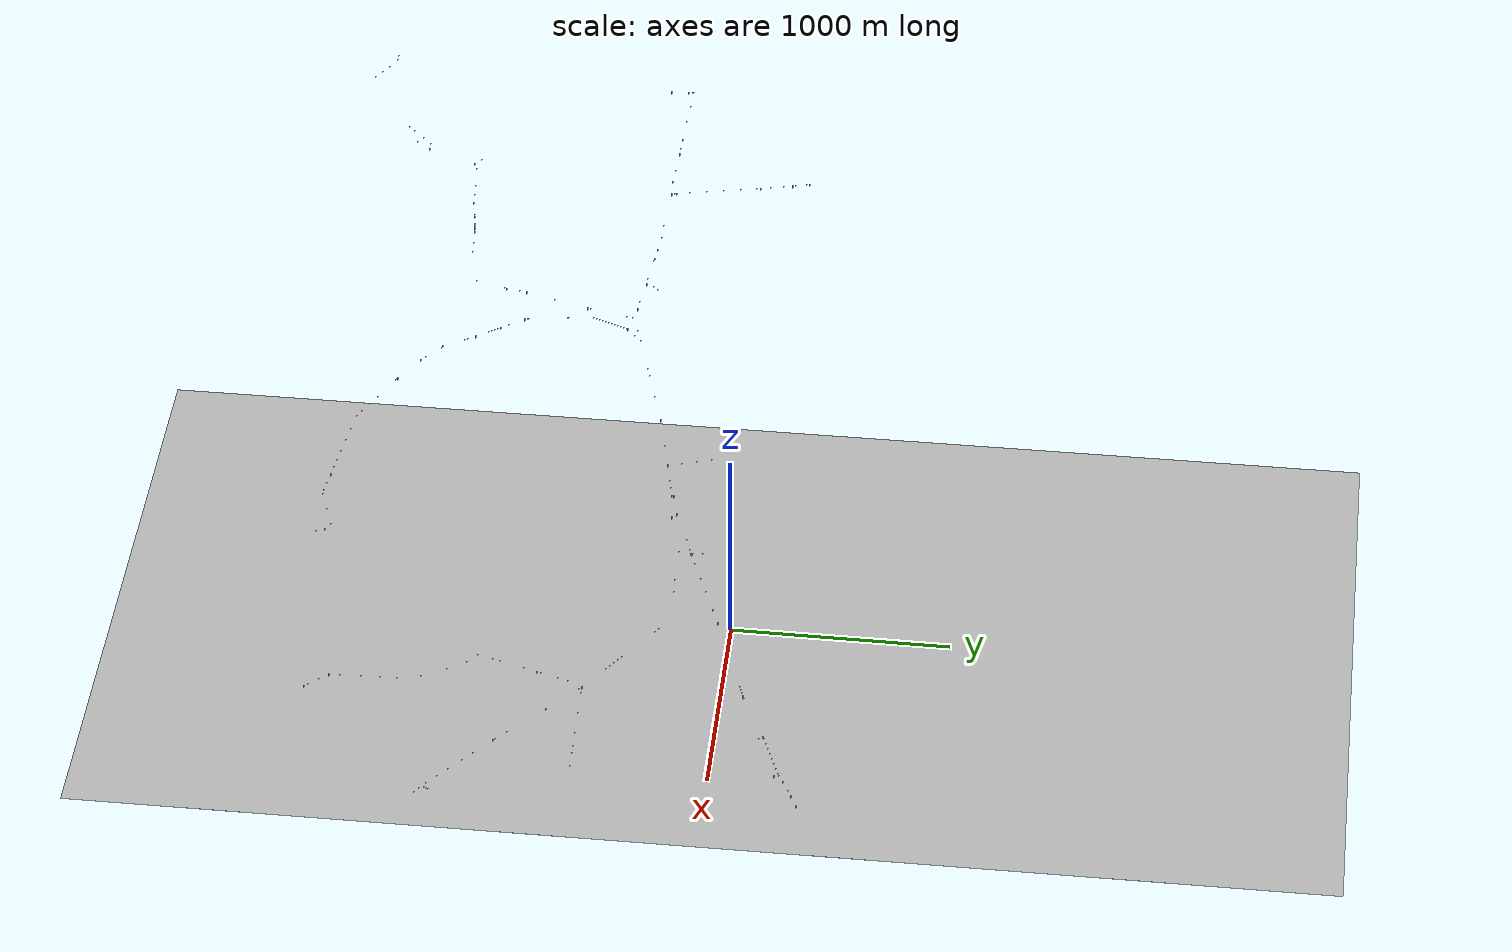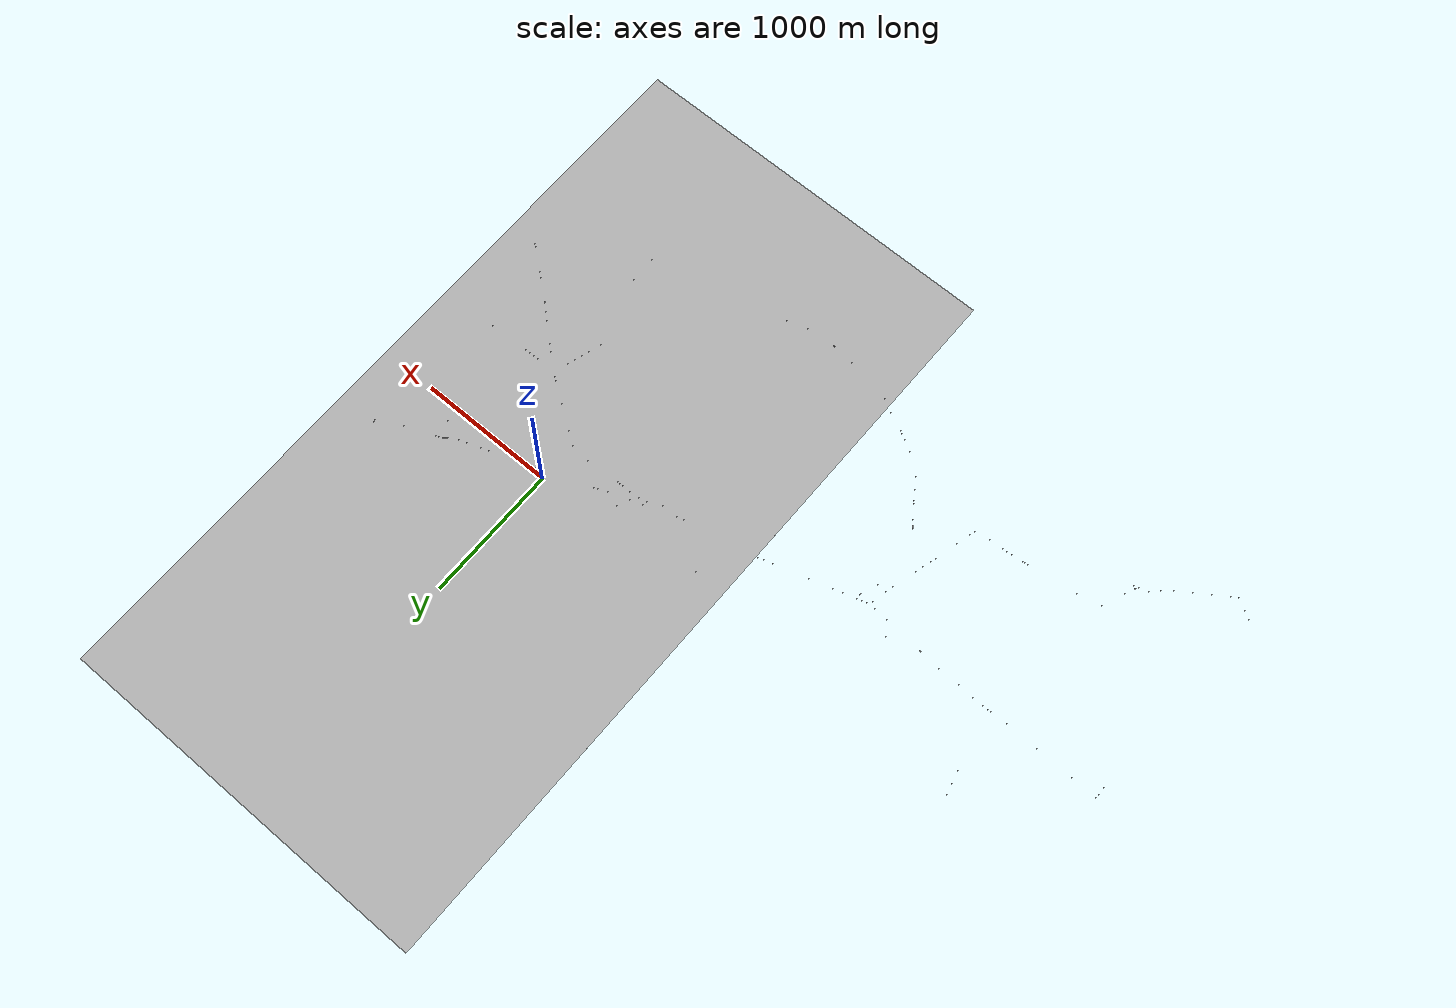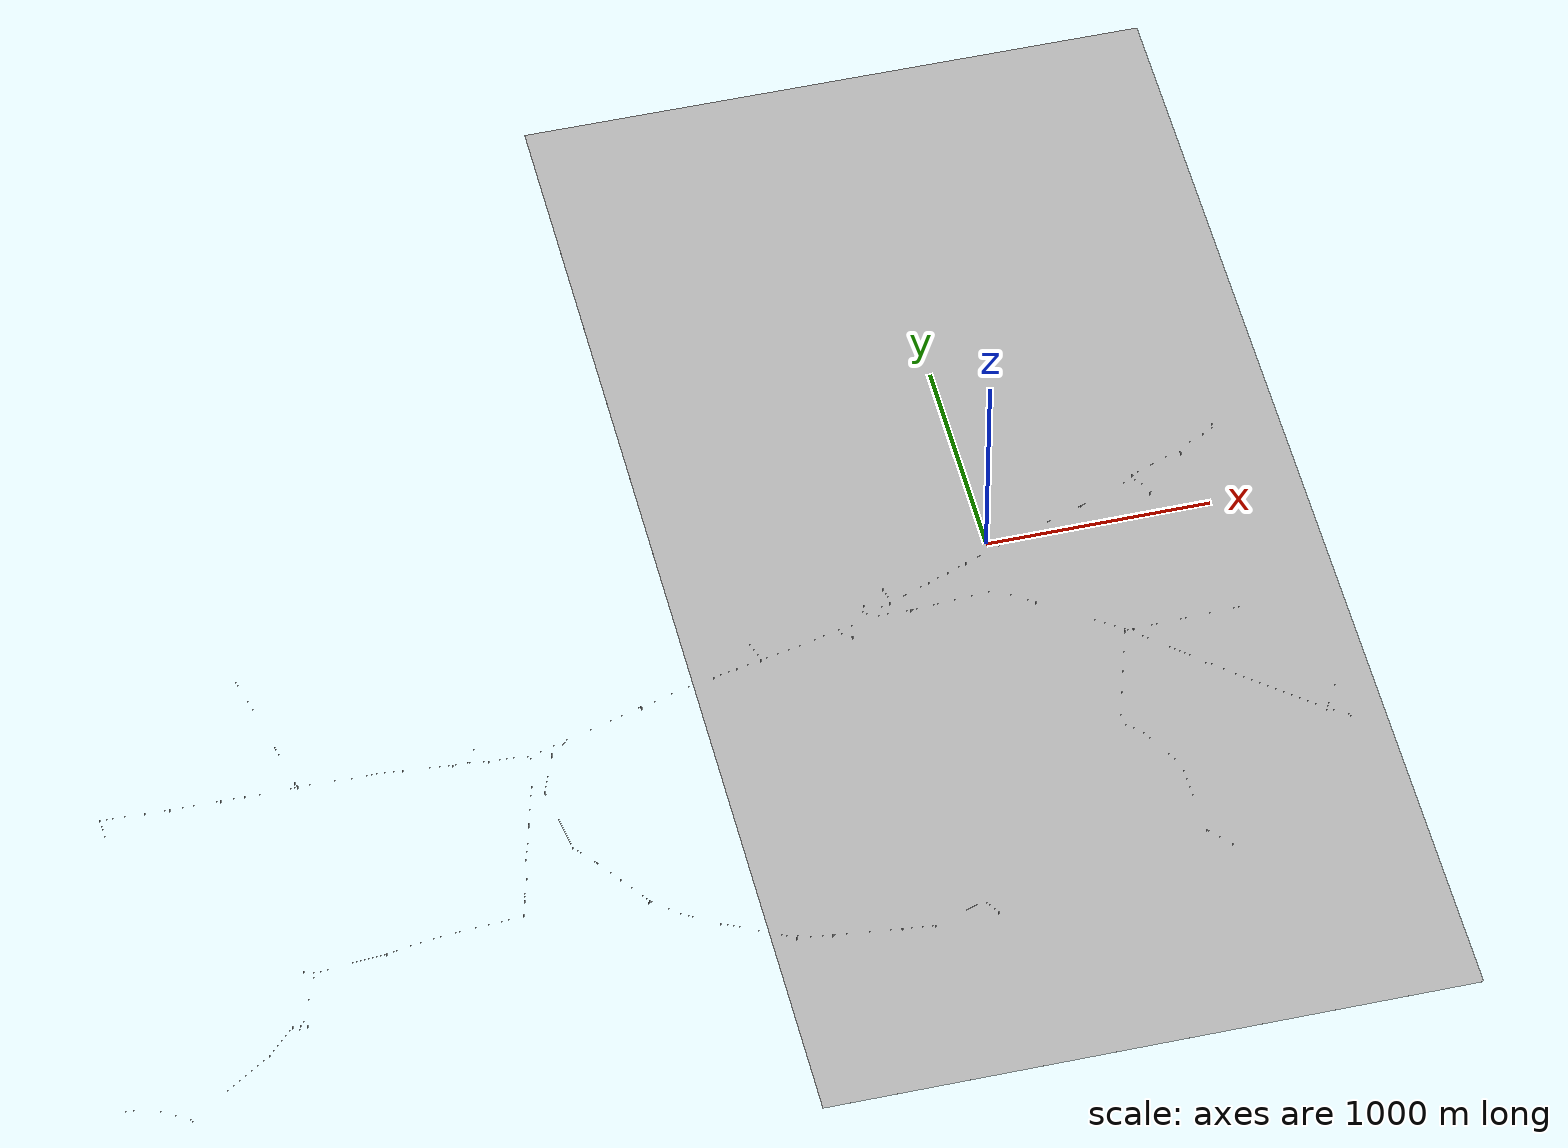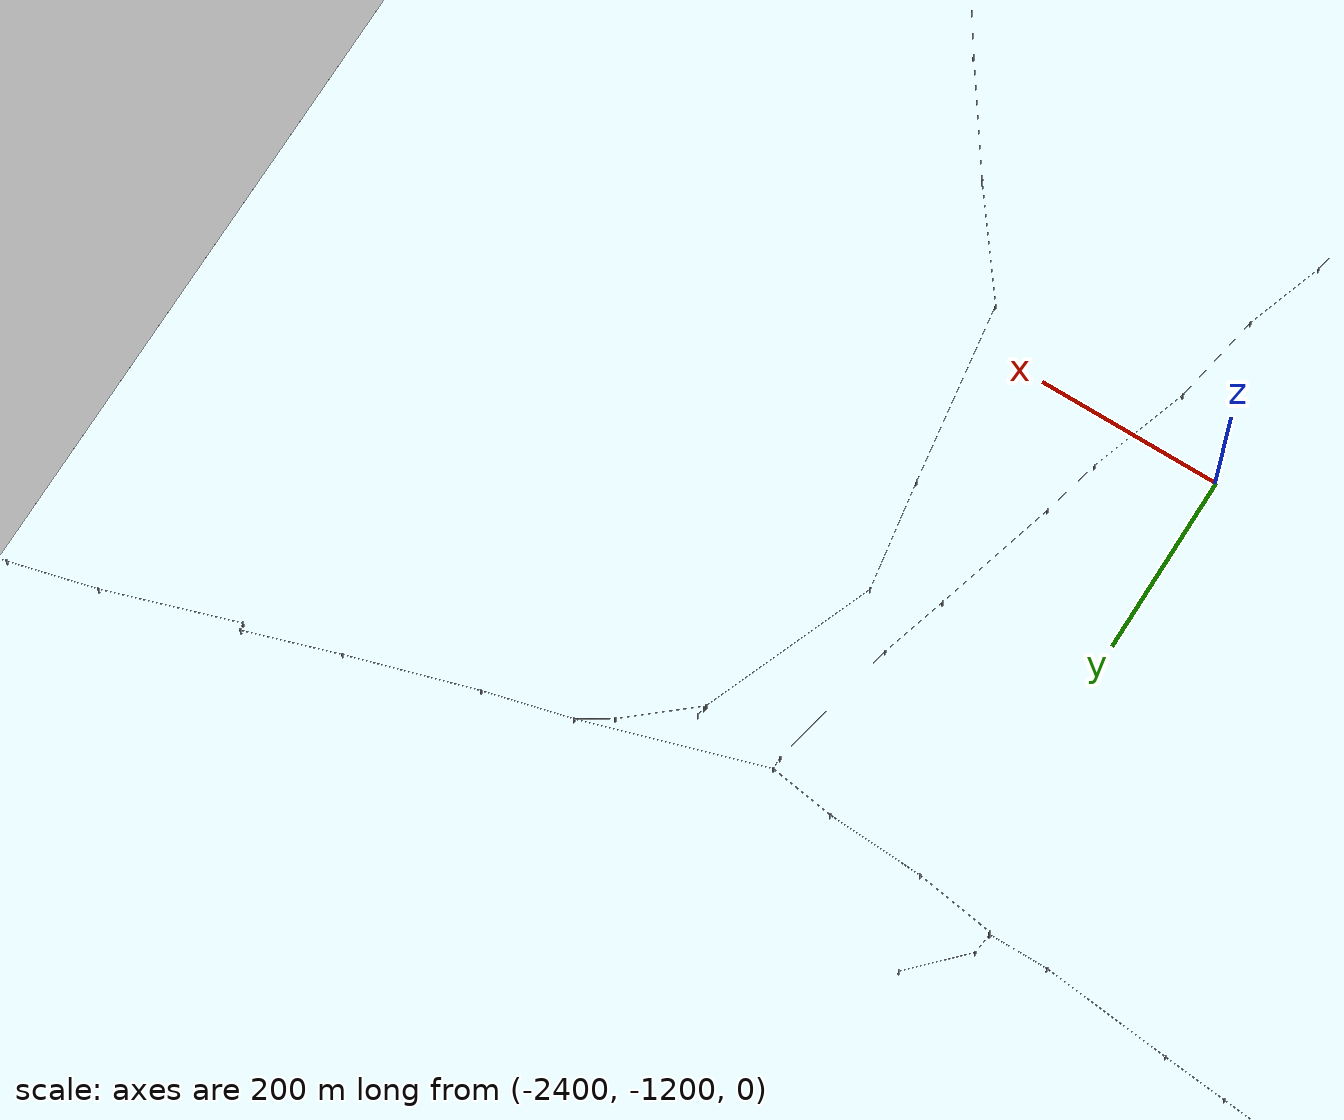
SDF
<sdf version="1.4">
 <world name="ATLAS_power_lines_world_big">
  <physics type="ode">
   <ode>
    <solver><type>quick</type><iters>10</iters><sor>1.3</sor></solver>
    <constraints>
     <cfm>0</cfm>
     <erp>0.2</erp>
     <contact_max_correcting_vel>100</contact_max_correcting_vel>
     <contact_surface_layer>0.001</contact_surface_layer>
    </constraints>
   </ode>
   <max_step_size>0.004</max_step_size>
   <real_time_factor>1</real_time_factor>
   <real_time_update_rate>250</real_time_update_rate>
   <gravity>0 0 -9.8</gravity>
   <magnetic_field>6e-06 2.3e-05 -4.2e-05</magnetic_field>
  </physics>
  <include><uri>model://ATLAS_ground_big</uri></include>
  <include><uri>model://sun</uri></include>
  <include>
   <uri>model://charging_pad_bolognini_s1</uri>
   <pose>28 61 0 0 0 1.895919</pose>
   <name>charging_pad</name>
  </include>
  <model name="Pylon_low_res_1">
   <static>1</static>
   <link name="link">
    <visual name="visual">
     <cast_shadows>false</cast_shadows>
     <geometry><cylinder><radius>0.75</radius><length>15</length></cylinder></geometry>
    </visual>
   </link>
   <pose>-4222.451 -2178.619 7.5 0 0 0</pose>
  </model>
  <model name="Pylon_low_res_2">
   <static>1</static>
   <link name="link">
    <visual name="visual">
     <cast_shadows>false</cast_shadows>
     <geometry><cylinder><radius>0.75</radius><length>15</length></cylinder></geometry>
    </visual>
   </link>
   <pose>-4132.362 -2178.62 7.5 0 0 0</pose>
  </model>
  <model name="Pylon_low_res_3">
   <static>1</static>
   <link name="link">
    <visual name="visual">
     <cast_shadows>false</cast_shadows>
     <geometry><cylinder><radius>0.75</radius><length>15</length></cylinder></geometry>
    </visual>
   </link>
   <pose>-4030.025 -631.153 7.5 0 0 0</pose>
  </model>
  <model name="Pylon_low_res_4">
   <static>1</static>
   <link name="link">
    <visual name="visual">
     <cast_shadows>false</cast_shadows>
     <geometry><cylinder><radius>0.75</radius><length>15</length></cylinder></geometry>
    </visual>
   </link>
   <pose>-4029.286 -641.126 7.5 0 0 0</pose>
  </model>
  <model name="Pylon_low_res_5">
   <static>1</static>
   <link name="link">
    <visual name="visual">
     <cast_shadows>false</cast_shadows>
     <geometry><cylinder><radius>0.75</radius><length>15</length></cylinder></geometry>
    </visual>
   </link>
   <pose>-4028.026 -658.153 7.5 0 0 0</pose>
  </model>
  <model name="Pylon_low_res_6">
   <static>1</static>
   <link name="link">
    <visual name="visual">
     <cast_shadows>false</cast_shadows>
     <geometry><cylinder><radius>0.75</radius><length>15</length></cylinder></geometry>
    </visual>
   </link>
   <pose>-4025.595 -744.627 7.5 0 0 0</pose>
  </model>
  <model name="Pylon_low_res_7">
   <static>1</static>
   <link name="link">
    <visual name="visual">
     <cast_shadows>false</cast_shadows>
     <geometry><cylinder><radius>0.75</radius><length>15</length></cylinder></geometry>
    </visual>
   </link>
   <pose>-3963.448 -2283.725 7.5 0 0 0</pose>
  </model>
  <model name="Pylon_low_res_8">
   <static>1</static>
   <link name="link">
    <visual name="visual">
     <cast_shadows>false</cast_shadows>
     <geometry><cylinder><radius>0.75</radius><length>15</length></cylinder></geometry>
    </visual>
   </link>
   <pose>-3950.727 -632.099 7.5 0 0 0</pose>
  </model>
  <model name="Pylon_low_res_9">
   <static>1</static>
   <link name="link">
    <visual name="visual">
     <cast_shadows>false</cast_shadows>
     <geometry><cylinder><radius>0.75</radius><length>15</length></cylinder></geometry>
    </visual>
   </link>
   <pose>-3838.8 -636.781 7.5 0 0 0</pose>
  </model>
  <model name="Pylon_low_res_10">
   <static>1</static>
   <link name="link">
    <visual name="visual">
     <cast_shadows>false</cast_shadows>
     <geometry><cylinder><radius>0.75</radius><length>15</length></cylinder></geometry>
    </visual>
   </link>
   <pose>-3731.743 -641.908 7.5 0 0 0</pose>
  </model>
  <model name="Pylon_low_res_11">
   <static>1</static>
   <link name="link">
    <visual name="visual">
     <cast_shadows>false</cast_shadows>
     <geometry><cylinder><radius>0.75</radius><length>15</length></cylinder></geometry>
    </visual>
   </link>
   <pose>-3631.206 -642.7 7.5 0 0 0</pose>
  </model>
  <model name="Pylon_low_res_12">
   <static>1</static>
   <link name="link">
    <visual name="visual">
     <cast_shadows>false</cast_shadows>
     <geometry><cylinder><radius>0.75</radius><length>15</length></cylinder></geometry>
    </visual>
   </link>
   <pose>-3586.001 -2029.255 7.5 0 0 0</pose>
  </model>
  <model name="Pylon_low_res_13">
   <static>1</static>
   <link name="link">
    <visual name="visual">
     <cast_shadows>false</cast_shadows>
     <geometry><cylinder><radius>0.75</radius><length>15</length></cylinder></geometry>
    </visual>
   </link>
   <pose>-3511.51 -644.344 7.5 0 0 0</pose>
  </model>
  <model name="Pylon_low_res_14">
   <static>1</static>
   <link name="link">
    <visual name="visual">
     <cast_shadows>false</cast_shadows>
     <geometry><cylinder><radius>0.75</radius><length>15</length></cylinder></geometry>
    </visual>
   </link>
   <pose>-3479.855 -1974.146 7.5 0 0 0</pose>
  </model>
  <model name="Pylon_low_res_15">
   <static>1</static>
   <link name="link">
    <visual name="visual">
     <cast_shadows>false</cast_shadows>
     <geometry><cylinder><radius>0.75</radius><length>15</length></cylinder></geometry>
    </visual>
   </link>
   <pose>-3462.443 -1903.775 7.5 0 0 0</pose>
  </model>
  <model name="Pylon_low_res_16">
   <static>1</static>
   <link name="link">
    <visual name="visual">
     <cast_shadows>false</cast_shadows>
     <geometry><cylinder><radius>0.75</radius><length>15</length></cylinder></geometry>
    </visual>
   </link>
   <pose>-3428.446 -1903.266 7.5 0 0 0</pose>
  </model>
  <model name="Pylon_low_res_17">
   <static>1</static>
   <link name="link">
    <visual name="visual">
     <cast_shadows>false</cast_shadows>
     <geometry><cylinder><radius>0.75</radius><length>15</length></cylinder></geometry>
    </visual>
   </link>
   <pose>-3418.447 -1903.116 7.5 0 0 0</pose>
  </model>
  <model name="Pylon_low_res_18">
   <static>1</static>
   <link name="link">
    <visual name="visual">
     <cast_shadows>false</cast_shadows>
     <geometry><cylinder><radius>0.75</radius><length>15</length></cylinder></geometry>
    </visual>
   </link>
   <pose>-3407.693 -645.406 7.5 0 0 0</pose>
  </model>
  <model name="Pylon_low_res_19">
   <static>1</static>
   <link name="link">
    <visual name="visual">
     <cast_shadows>false</cast_shadows>
     <geometry><cylinder><radius>0.75</radius><length>15</length></cylinder></geometry>
    </visual>
   </link>
   <pose>-3400.896 -1913.6 7.5 0 0 0</pose>
  </model>
  <model name="Pylon_low_res_20">
   <static>1</static>
   <link name="link">
    <visual name="visual">
     <cast_shadows>false</cast_shadows>
     <geometry><cylinder><radius>0.75</radius><length>15</length></cylinder></geometry>
    </visual>
   </link>
   <pose>-3374.302 -1793.215 7.5 0 0 0</pose>
  </model>
  <model name="Pylon_low_res_21">
   <static>1</static>
   <link name="link">
    <visual name="visual">
     <cast_shadows>false</cast_shadows>
     <geometry><cylinder><radius>0.75</radius><length>15</length></cylinder></geometry>
    </visual>
   </link>
   <pose>-3357.904 -1627.72 7.5 0 0 0</pose>
  </model>
  <model name="Pylon_low_res_22">
   <static>1</static>
   <link name="link">
    <visual name="visual">
     <cast_shadows>false</cast_shadows>
     <geometry><cylinder><radius>0.75</radius><length>15</length></cylinder></geometry>
    </visual>
   </link>
   <pose>-3332.604 32.362 7.5 0 0 0</pose>
  </model>
  <model name="Pylon_low_res_23">
   <static>1</static>
   <link name="link">
    <visual name="visual">
     <cast_shadows>false</cast_shadows>
     <geometry><cylinder><radius>0.75</radius><length>15</length></cylinder></geometry>
    </visual>
   </link>
   <pose>-3320.149 -1659.561 7.5 0 0 0</pose>
  </model>
  <model name="Pylon_low_res_24">
   <static>1</static>
   <link name="link">
    <visual name="visual">
     <cast_shadows>false</cast_shadows>
     <geometry><cylinder><radius>0.75</radius><length>15</length></cylinder></geometry>
    </visual>
   </link>
   <pose>-3310.604 -50.636 7.5 0 0 0</pose>
  </model>
  <model name="Pylon_low_res_25">
   <static>1</static>
   <link name="link">
    <visual name="visual">
     <cast_shadows>false</cast_shadows>
     <geometry><cylinder><radius>0.75</radius><length>15</length></cylinder></geometry>
    </visual>
   </link>
   <pose>-3308.929 -1646.654 7.5 0 0 0</pose>
  </model>
  <model name="Pylon_low_res_26">
   <static>1</static>
   <link name="link">
    <visual name="visual">
     <cast_shadows>false</cast_shadows>
     <geometry><cylinder><radius>0.75</radius><length>15</length></cylinder></geometry>
    </visual>
   </link>
   <pose>-3283.124 -653.128 7.5 0 0 0</pose>
  </model>
  <model name="Pylon_low_res_27">
   <static>1</static>
   <link name="link">
    <visual name="visual">
     <cast_shadows>false</cast_shadows>
     <geometry><cylinder><radius>0.75</radius><length>15</length></cylinder></geometry>
    </visual>
   </link>
   <pose>-3272.605 -208.633 7.5 0 0 0</pose>
  </model>
  <model name="Pylon_low_res_28">
   <static>1</static>
   <link name="link">
    <visual name="visual">
     <cast_shadows>false</cast_shadows>
     <geometry><cylinder><radius>0.75</radius><length>15</length></cylinder></geometry>
    </visual>
   </link>
   <pose>-3227.606 -423.631 7.5 0 0 0</pose>
  </model>
  <model name="Pylon_low_res_29">
   <static>1</static>
   <link name="link">
    <visual name="visual">
     <cast_shadows>false</cast_shadows>
     <geometry><cylinder><radius>0.75</radius><length>15</length></cylinder></geometry>
    </visual>
   </link>
   <pose>-3186.606 -620.629 7.5 0 0 0</pose>
  </model>
  <model name="Pylon_low_res_30">
   <static>1</static>
   <link name="link">
    <visual name="visual">
     <cast_shadows>false</cast_shadows>
     <geometry><cylinder><radius>0.75</radius><length>15</length></cylinder></geometry>
    </visual>
   </link>
   <pose>-3179.606 -645.629 7.5 0 0 0</pose>
  </model>
  <model name="Pylon_low_res_31">
   <static>1</static>
   <link name="link">
    <visual name="visual">
     <cast_shadows>false</cast_shadows>
     <geometry><cylinder><radius>0.75</radius><length>15</length></cylinder></geometry>
    </visual>
   </link>
   <pose>-3150.371 -1629.036 7.5 0 0 0</pose>
  </model>
  <model name="Pylon_low_res_32">
   <static>1</static>
   <link name="link">
    <visual name="visual">
     <cast_shadows>false</cast_shadows>
     <geometry><cylinder><radius>0.75</radius><length>15</length></cylinder></geometry>
    </visual>
   </link>
   <pose>-3059.884 -645.267 7.5 0 0 0</pose>
  </model>
  <model name="Pylon_low_res_33">
   <static>1</static>
   <link name="link">
    <visual name="visual">
     <cast_shadows>false</cast_shadows>
     <geometry><cylinder><radius>0.75</radius><length>15</length></cylinder></geometry>
    </visual>
   </link>
   <pose>-3002.203 -1618.081 7.5 0 0 0</pose>
  </model>
  <model name="Pylon_low_res_34">
   <static>1</static>
   <link name="link">
    <visual name="visual">
     <cast_shadows>false</cast_shadows>
     <geometry><cylinder><radius>0.75</radius><length>15</length></cylinder></geometry>
    </visual>
   </link>
   <pose>-2941.412 -655.502 7.5 0 0 0</pose>
  </model>
  <model name="Pylon_low_res_35">
   <static>1</static>
   <link name="link">
    <visual name="visual">
     <cast_shadows>false</cast_shadows>
     <geometry><cylinder><radius>0.75</radius><length>15</length></cylinder></geometry>
    </visual>
   </link>
   <pose>-2893.974 -1597.396 7.5 0 0 0</pose>
  </model>
  <model name="Pylon_low_res_36">
   <static>1</static>
   <link name="link">
    <visual name="visual">
     <cast_shadows>false</cast_shadows>
     <geometry><cylinder><radius>0.75</radius><length>15</length></cylinder></geometry>
    </visual>
   </link>
   <pose>-2833.139 -652.684 7.5 0 0 0</pose>
  </model>
  <model name="Pylon_low_res_37">
   <static>1</static>
   <link name="link">
    <visual name="visual">
     <cast_shadows>false</cast_shadows>
     <geometry><cylinder><radius>0.75</radius><length>15</length></cylinder></geometry>
    </visual>
   </link>
   <pose>-2772.622 -1580.566 7.5 0 0 0</pose>
  </model>
  <model name="Pylon_low_res_38">
   <static>1</static>
   <link name="link">
    <visual name="visual">
     <cast_shadows>false</cast_shadows>
     <geometry><cylinder><radius>0.75</radius><length>15</length></cylinder></geometry>
    </visual>
   </link>
   <pose>-2727.436 -662.57 7.5 0 0 0</pose>
  </model>
  <model name="Pylon_low_res_39">
   <static>1</static>
   <link name="link">
    <visual name="visual">
     <cast_shadows>false</cast_shadows>
     <geometry><cylinder><radius>0.75</radius><length>15</length></cylinder></geometry>
    </visual>
   </link>
   <pose>-2657.582 -669.005 7.5 0 0 0</pose>
  </model>
  <model name="Pylon_low_res_40">
   <static>1</static>
   <link name="link">
    <visual name="visual">
     <cast_shadows>false</cast_shadows>
     <geometry><cylinder><radius>0.75</radius><length>15</length></cylinder></geometry>
    </visual>
   </link>
   <pose>-2637.853 -1568.319 7.5 0 0 0</pose>
  </model>
  <model name="Pylon_low_res_41">
   <static>1</static>
   <link name="link">
    <visual name="visual">
     <cast_shadows>false</cast_shadows>
     <geometry><cylinder><radius>0.75</radius><length>15</length></cylinder></geometry>
    </visual>
   </link>
   <pose>-2515.411 -683.495 7.5 0 0 0</pose>
  </model>
  <model name="Pylon_low_res_42">
   <static>1</static>
   <link name="link">
    <visual name="visual">
     <cast_shadows>false</cast_shadows>
     <geometry><cylinder><radius>0.75</radius><length>15</length></cylinder></geometry>
    </visual>
   </link>
   <pose>-2493.476 -1561.155 7.5 0 0 0</pose>
  </model>
  <model name="Pylon_low_res_43">
   <static>1</static>
   <link name="link">
    <visual name="visual">
     <cast_shadows>false</cast_shadows>
     <geometry><cylinder><radius>0.75</radius><length>15</length></cylinder></geometry>
    </visual>
   </link>
   <pose>-2450.644 -683.145 7.5 0 0 0</pose>
  </model>
  <model name="Pylon_low_res_44">
   <static>1</static>
   <link name="link">
    <visual name="visual">
     <cast_shadows>false</cast_shadows>
     <geometry><cylinder><radius>0.75</radius><length>15</length></cylinder></geometry>
    </visual>
   </link>
   <pose>-2449.14 -685.374 7.5 0 0 0</pose>
  </model>
  <model name="Pylon_low_res_45">
   <static>1</static>
   <link name="link">
    <visual name="visual">
     <cast_shadows>false</cast_shadows>
     <geometry><cylinder><radius>0.75</radius><length>15</length></cylinder></geometry>
    </visual>
   </link>
   <pose>-2448.073 -660.457 7.5 0 0 0</pose>
  </model>
  <model name="Pylon_low_res_46">
   <static>1</static>
   <link name="link">
    <visual name="visual">
     <cast_shadows>false</cast_shadows>
     <geometry><cylinder><radius>0.75</radius><length>15</length></cylinder></geometry>
    </visual>
   </link>
   <pose>-2399.065 -1549.254 7.5 0 0 0</pose>
  </model>
  <model name="Pylon_low_res_47">
   <static>1</static>
   <link name="link">
    <visual name="visual">
     <cast_shadows>false</cast_shadows>
     <geometry><cylinder><radius>0.75</radius><length>15</length></cylinder></geometry>
    </visual>
   </link>
   <pose>-2395.128 -604.979 7.5 0 0 0</pose>
  </model>
  <model name="Pylon_low_res_48">
   <static>1</static>
   <link name="link">
    <visual name="visual">
     <cast_shadows>false</cast_shadows>
     <geometry><cylinder><radius>0.75</radius><length>15</length></cylinder></geometry>
    </visual>
   </link>
   <pose>-2385.874 -1511.312 7.5 0 0 0</pose>
  </model>
  <model name="Pylon_low_res_49">
   <static>1</static>
   <link name="link">
    <visual name="visual">
     <cast_shadows>false</cast_shadows>
     <geometry><cylinder><radius>0.75</radius><length>15</length></cylinder></geometry>
    </visual>
   </link>
   <pose>-2372.988 -1445.972 7.5 0 0 0</pose>
  </model>
  <model name="Pylon_low_res_50">
   <static>1</static>
   <link name="link">
    <visual name="visual">
     <cast_shadows>false</cast_shadows>
     <geometry><cylinder><radius>0.75</radius><length>15</length></cylinder></geometry>
    </visual>
   </link>
   <pose>-2362.378 -697.961 7.5 0 0 0</pose>
  </model>
  <model name="Pylon_low_res_51">
   <static>1</static>
   <link name="link">
    <visual name="visual">
     <cast_shadows>false</cast_shadows>
     <geometry><cylinder><radius>0.75</radius><length>15</length></cylinder></geometry>
    </visual>
   </link>
   <pose>-2344.289 -1360.288 7.5 0 0 0</pose>
  </model>
  <model name="Pylon_low_res_52">
   <static>1</static>
   <link name="link">
    <visual name="visual">
     <cast_shadows>false</cast_shadows>
     <geometry><cylinder><radius>0.75</radius><length>15</length></cylinder></geometry>
    </visual>
   </link>
   <pose>-2326.189 -1259.26 7.5 0 0 0</pose>
  </model>
  <model name="Pylon_low_res_53">
   <static>1</static>
   <link name="link">
    <visual name="visual">
     <cast_shadows>false</cast_shadows>
     <geometry><cylinder><radius>0.75</radius><length>15</length></cylinder></geometry>
    </visual>
   </link>
   <pose>-2289.802 -1148.681 7.5 0 0 0</pose>
  </model>
  <model name="Pylon_low_res_54">
   <static>1</static>
   <link name="link">
    <visual name="visual">
     <cast_shadows>false</cast_shadows>
     <geometry><cylinder><radius>0.75</radius><length>15</length></cylinder></geometry>
    </visual>
   </link>
   <pose>-2274.393 -1083.768 7.5 0 0 0</pose>
  </model>
  <model name="Pylon_low_res_55">
   <static>1</static>
   <link name="link">
    <visual name="visual">
     <cast_shadows>false</cast_shadows>
     <geometry><cylinder><radius>0.75</radius><length>15</length></cylinder></geometry>
    </visual>
   </link>
   <pose>-2256.166 -703.33 7.5 0 0 0</pose>
  </model>
  <model name="Pylon_low_res_56">
   <static>1</static>
   <link name="link">
    <visual name="visual">
     <cast_shadows>false</cast_shadows>
     <geometry><cylinder><radius>0.75</radius><length>15</length></cylinder></geometry>
    </visual>
   </link>
   <pose>-2236.082 -947.377 7.5 0 0 0</pose>
  </model>
  <model name="Pylon_low_res_57">
   <static>1</static>
   <link name="link">
    <visual name="visual">
     <cast_shadows>false</cast_shadows>
     <geometry><cylinder><radius>0.75</radius><length>15</length></cylinder></geometry>
    </visual>
   </link>
   <pose>-2214.664 -873.946 7.5 0 0 0</pose>
  </model>
  <model name="Pylon_low_res_58">
   <static>1</static>
   <link name="link">
    <visual name="visual">
     <cast_shadows>false</cast_shadows>
     <geometry><cylinder><radius>0.75</radius><length>15</length></cylinder></geometry>
    </visual>
   </link>
   <pose>-2184.567 -713.625 7.5 0 0 0</pose>
  </model>
  <model name="Pylon_low_res_59">
   <static>1</static>
   <link name="link">
    <visual name="visual">
     <cast_shadows>false</cast_shadows>
     <geometry><cylinder><radius>0.75</radius><length>15</length></cylinder></geometry>
    </visual>
   </link>
   <pose>-2184.477 -726.603 7.5 0 0 0</pose>
  </model>
  <model name="Pylon_low_res_60">
   <static>1</static>
   <link name="link">
    <visual name="visual">
     <cast_shadows>false</cast_shadows>
     <geometry><cylinder><radius>0.75</radius><length>15</length></cylinder></geometry>
    </visual>
   </link>
   <pose>-2168.496 -920.5 7.5 0 0 0</pose>
  </model>
  <model name="Pylon_low_res_61">
   <static>1</static>
   <link name="link">
    <visual name="visual">
     <cast_shadows>false</cast_shadows>
     <geometry><cylinder><radius>0.75</radius><length>15</length></cylinder></geometry>
    </visual>
   </link>
   <pose>-2148.897 -1040.636 7.5 0 0 0</pose>
  </model>
  <model name="Pylon_low_res_62">
   <static>1</static>
   <link name="link">
    <visual name="visual">
     <cast_shadows>false</cast_shadows>
     <geometry><cylinder><radius>0.75</radius><length>15</length></cylinder></geometry>
    </visual>
   </link>
   <pose>-2119.091 -1240.634 7.5 0 0 0</pose>
  </model>
  <model name="Pylon_low_res_63">
   <static>1</static>
   <link name="link">
    <visual name="visual">
     <cast_shadows>false</cast_shadows>
     <geometry><cylinder><radius>0.75</radius><length>15</length></cylinder></geometry>
    </visual>
   </link>
   <pose>-2095.076 -733.158 7.5 0 0 0</pose>
  </model>
  <model name="Pylon_low_res_64">
   <static>1</static>
   <link name="link">
    <visual name="visual">
     <cast_shadows>false</cast_shadows>
     <geometry><cylinder><radius>0.75</radius><length>15</length></cylinder></geometry>
    </visual>
   </link>
   <pose>-2094.589 -730.198 7.5 0 0 0</pose>
  </model>
  <model name="Pylon_low_res_65">
   <static>1</static>
   <link name="link">
    <visual name="visual">
     <cast_shadows>false</cast_shadows>
     <geometry><cylinder><radius>0.75</radius><length>15</length></cylinder></geometry>
    </visual>
   </link>
   <pose>-2093.103 -721.169 7.5 0 0 0</pose>
  </model>
  <model name="Pylon_low_res_66">
   <static>1</static>
   <link name="link">
    <visual name="visual">
     <cast_shadows>false</cast_shadows>
     <geometry><cylinder><radius>0.75</radius><length>15</length></cylinder></geometry>
    </visual>
   </link>
   <pose>-2038.547 -1347.157 7.5 0 0 0</pose>
  </model>
  <model name="Pylon_low_res_67">
   <static>1</static>
   <link name="link">
    <visual name="visual">
     <cast_shadows>false</cast_shadows>
     <geometry><cylinder><radius>0.75</radius><length>15</length></cylinder></geometry>
    </visual>
   </link>
   <pose>-2026.709 -674.771 7.5 0 0 0</pose>
  </model>
  <model name="Pylon_low_res_68">
   <static>1</static>
   <link name="link">
    <visual name="visual">
     <cast_shadows>false</cast_shadows>
     <geometry><cylinder><radius>0.75</radius><length>15</length></cylinder></geometry>
    </visual>
   </link>
   <pose>-1992.377 -653.073 7.5 0 0 0</pose>
  </model>
  <model name="Pylon_low_res_69">
   <static>1</static>
   <link name="link">
    <visual name="visual">
     <cast_shadows>false</cast_shadows>
     <geometry><cylinder><radius>0.75</radius><length>15</length></cylinder></geometry>
    </visual>
   </link>
   <pose>-1961.076 -1458.349 7.5 0 0 0</pose>
  </model>
  <model name="Pylon_low_res_70">
   <static>1</static>
   <link name="link">
    <visual name="visual">
     <cast_shadows>false</cast_shadows>
     <geometry><cylinder><radius>0.75</radius><length>15</length></cylinder></geometry>
    </visual>
   </link>
   <pose>-1899.613 -629.023 7.5 0 0 0</pose>
  </model>
  <model name="Pylon_low_res_71">
   <static>1</static>
   <link name="link">
    <visual name="visual">
     <cast_shadows>false</cast_shadows>
     <geometry><cylinder><radius>0.75</radius><length>15</length></cylinder></geometry>
    </visual>
   </link>
   <pose>-1874.124 -1606.555 7.5 0 0 0</pose>
  </model>
  <model name="Pylon_low_res_72">
   <static>1</static>
   <link name="link">
    <visual name="visual">
     <cast_shadows>false</cast_shadows>
     <geometry><cylinder><radius>0.75</radius><length>15</length></cylinder></geometry>
    </visual>
   </link>
   <pose>-1867.833 -1598.355 7.5 0 0 0</pose>
  </model>
  <model name="Pylon_low_res_73">
   <static>1</static>
   <link name="link">
    <visual name="visual">
     <cast_shadows>false</cast_shadows>
     <geometry><cylinder><radius>0.75</radius><length>15</length></cylinder></geometry>
    </visual>
   </link>
   <pose>-1764.195 -587.707 7.5 0 0 0</pose>
  </model>
  <model name="Pylon_low_res_74">
   <static>1</static>
   <link name="link">
    <visual name="visual">
     <cast_shadows>false</cast_shadows>
     <geometry><cylinder><radius>0.75</radius><length>15</length></cylinder></geometry>
    </visual>
   </link>
   <pose>-1755.219 -1697.212 7.5 0 0 0</pose>
  </model>
  <model name="Pylon_low_res_75">
   <static>1</static>
   <link name="link">
    <visual name="visual">
     <cast_shadows>false</cast_shadows>
     <geometry><cylinder><radius>0.75</radius><length>15</length></cylinder></geometry>
    </visual>
   </link>
   <pose>-1665.657 -555.446 7.5 0 0 0</pose>
  </model>
  <model name="Pylon_low_res_76">
   <static>1</static>
   <link name="link">
    <visual name="visual">
     <cast_shadows>false</cast_shadows>
     <geometry><cylinder><radius>0.75</radius><length>15</length></cylinder></geometry>
    </visual>
   </link>
   <pose>-1663.634 -562.797 7.5 0 0 0</pose>
  </model>
  <model name="Pylon_low_res_77">
   <static>1</static>
   <link name="link">
    <visual name="visual">
     <cast_shadows>false</cast_shadows>
     <geometry><cylinder><radius>0.75</radius><length>15</length></cylinder></geometry>
    </visual>
   </link>
   <pose>-1606.724 -1785.8 7.5 0 0 0</pose>
  </model>
  <model name="Pylon_low_res_78">
   <static>1</static>
   <link name="link">
    <visual name="visual">
     <cast_shadows>false</cast_shadows>
     <geometry><cylinder><radius>0.75</radius><length>15</length></cylinder></geometry>
    </visual>
   </link>
   <pose>-1523.514 -516.546 7.5 0 0 0</pose>
  </model>
  <model name="Pylon_low_res_79">
   <static>1</static>
   <link name="link">
    <visual name="visual">
     <cast_shadows>false</cast_shadows>
     <geometry><cylinder><radius>0.75</radius><length>15</length></cylinder></geometry>
    </visual>
   </link>
   <pose>-1493.935 -1882.216 7.5 0 0 0</pose>
  </model>
  <model name="Pylon_low_res_80">
   <static>1</static>
   <link name="link">
    <visual name="visual">
     <cast_shadows>false</cast_shadows>
     <geometry><cylinder><radius>0.75</radius><length>15</length></cylinder></geometry>
    </visual>
   </link>
   <pose>-1456.758 -1858.442 7.5 0 0 0</pose>
  </model>
  <model name="Pylon_low_res_81">
   <static>1</static>
   <link name="link">
    <visual name="visual">
     <cast_shadows>false</cast_shadows>
     <geometry><cylinder><radius>0.75</radius><length>15</length></cylinder></geometry>
    </visual>
   </link>
   <pose>-1430.835 -492.496 7.5 0 0 0</pose>
  </model>
  <model name="Pylon_low_res_82">
   <static>1</static>
   <link name="link">
    <visual name="visual">
     <cast_shadows>false</cast_shadows>
     <geometry><cylinder><radius>0.75</radius><length>15</length></cylinder></geometry>
    </visual>
   </link>
   <pose>-1325.945 -469.053 7.5 0 0 0</pose>
  </model>
  <model name="Pylon_low_res_83">
   <static>1</static>
   <link name="link">
    <visual name="visual">
     <cast_shadows>false</cast_shadows>
     <geometry><cylinder><radius>0.75</radius><length>15</length></cylinder></geometry>
    </visual>
   </link>
   <pose>-1314.445 -1935.237 7.5 0 0 0</pose>
  </model>
  <model name="Pylon_low_res_84">
   <static>1</static>
   <link name="link">
    <visual name="visual">
     <cast_shadows>false</cast_shadows>
     <geometry><cylinder><radius>0.75</radius><length>15</length></cylinder></geometry>
    </visual>
   </link>
   <pose>-1304.038 -1918.157 7.5 0 0 0</pose>
  </model>
  <model name="Pylon_low_res_85">
   <static>1</static>
   <link name="link">
    <visual name="visual">
     <cast_shadows>false</cast_shadows>
     <geometry><cylinder><radius>0.75</radius><length>15</length></cylinder></geometry>
    </visual>
   </link>
   <pose>-1219.436 -445.978 7.5 0 0 0</pose>
  </model>
  <model name="Pylon_low_res_86">
   <static>1</static>
   <link name="link">
    <visual name="visual">
     <cast_shadows>false</cast_shadows>
     <geometry><cylinder><radius>0.75</radius><length>15</length></cylinder></geometry>
    </visual>
   </link>
   <pose>-1189.809 -152.514 7.5 0 0 0</pose>
  </model>
  <model name="Pylon_low_res_87">
   <static>1</static>
   <link name="link">
    <visual name="visual">
     <cast_shadows>false</cast_shadows>
     <geometry><cylinder><radius>0.75</radius><length>15</length></cylinder></geometry>
    </visual>
   </link>
   <pose>-1164.946 -1955.25 7.5 0 0 0</pose>
  </model>
  <model name="Pylon_low_res_88">
   <static>1</static>
   <link name="link">
    <visual name="visual">
     <cast_shadows>false</cast_shadows>
     <geometry><cylinder><radius>0.75</radius><length>15</length></cylinder></geometry>
    </visual>
   </link>
   <pose>-1111.243 -395.872 7.5 0 0 0</pose>
  </model>
  <model name="Pylon_low_res_89">
   <static>1</static>
   <link name="link">
    <visual name="visual">
     <cast_shadows>false</cast_shadows>
     <geometry><cylinder><radius>0.75</radius><length>15</length></cylinder></geometry>
    </visual>
   </link>
   <pose>-1107.013 -421.726 7.5 0 0 0</pose>
  </model>
  <model name="Pylon_low_res_90">
   <static>1</static>
   <link name="link">
    <visual name="visual">
     <cast_shadows>false</cast_shadows>
     <geometry><cylinder><radius>0.75</radius><length>15</length></cylinder></geometry>
    </visual>
   </link>
   <pose>-1019.38 -1973.884 7.5 0 0 0</pose>
  </model>
  <model name="Pylon_low_res_91">
   <static>1</static>
   <link name="link">
    <visual name="visual">
     <cast_shadows>false</cast_shadows>
     <geometry><cylinder><radius>0.75</radius><length>15</length></cylinder></geometry>
    </visual>
   </link>
   <pose>-887.529 -366.336 7.5 0 0 0</pose>
  </model>
  <model name="Pylon_low_res_92">
   <static>1</static>
   <link name="link">
    <visual name="visual">
     <cast_shadows>false</cast_shadows>
     <geometry><cylinder><radius>0.75</radius><length>15</length></cylinder></geometry>
    </visual>
   </link>
   <pose>-886.759 -375.461 7.5 0 0 0</pose>
  </model>
  <model name="Pylon_low_res_93">
   <static>1</static>
   <link name="link">
    <visual name="visual">
     <cast_shadows>false</cast_shadows>
     <geometry><cylinder><radius>0.75</radius><length>15</length></cylinder></geometry>
    </visual>
   </link>
   <pose>-871.444 -1991.265 7.5 0 0 0</pose>
  </model>
  <model name="Pylon_low_res_94">
   <static>1</static>
   <link name="link">
    <visual name="visual">
     <cast_shadows>false</cast_shadows>
     <geometry><cylinder><radius>0.75</radius><length>15</length></cylinder></geometry>
    </visual>
   </link>
   <pose>-766.971 -339.191 7.5 0 0 0</pose>
  </model>
  <model name="Pylon_low_res_95">
   <static>1</static>
   <link name="link">
    <visual name="visual">
     <cast_shadows>false</cast_shadows>
     <geometry><cylinder><radius>0.75</radius><length>15</length></cylinder></geometry>
    </visual>
   </link>
   <pose>-738.037 -358.049 7.5 0 0 0</pose>
  </model>
  <model name="Pylon_low_res_96">
   <static>1</static>
   <link name="link">
    <visual name="visual">
     <cast_shadows>false</cast_shadows>
     <geometry><cylinder><radius>0.75</radius><length>15</length></cylinder></geometry>
    </visual>
   </link>
   <pose>-733.149 -2007.442 7.5 0 0 0</pose>
  </model>
  <model name="Pylon_low_res_97">
   <static>1</static>
   <link name="link">
    <visual name="visual">
     <cast_shadows>false</cast_shadows>
     <geometry><cylinder><radius>0.75</radius><length>15</length></cylinder></geometry>
    </visual>
   </link>
   <pose>-694.034 -389.265 7.5 0 0 0</pose>
  </model>
  <model name="Pylon_low_res_98">
   <static>1</static>
   <link name="link">
    <visual name="visual">
     <cast_shadows>false</cast_shadows>
     <geometry><cylinder><radius>0.75</radius><length>15</length></cylinder></geometry>
    </visual>
   </link>
   <pose>-632.872 -319.215 7.5 0 0 0</pose>
  </model>
  <model name="Pylon_low_res_99">
   <static>1</static>
   <link name="link">
    <visual name="visual">
     <cast_shadows>false</cast_shadows>
     <geometry><cylinder><radius>0.75</radius><length>15</length></cylinder></geometry>
    </visual>
   </link>
   <pose>-626.517 -283.636 7.5 0 0 0</pose>
  </model>
  <model name="Pylon_low_res_100">
   <static>1</static>
   <link name="link">
    <visual name="visual">
     <cast_shadows>false</cast_shadows>
     <geometry><cylinder><radius>0.75</radius><length>15</length></cylinder></geometry>
    </visual>
   </link>
   <pose>-604.243 -227.165 7.5 0 0 0</pose>
  </model>
  <model name="Pylon_low_res_101">
   <static>1</static>
   <link name="link">
    <visual name="visual">
     <cast_shadows>false</cast_shadows>
     <geometry><cylinder><radius>0.75</radius><length>15</length></cylinder></geometry>
    </visual>
   </link>
   <pose>-544.652 -296.433 7.5 0 0 0</pose>
  </model>
  <model name="Pylon_low_res_102">
   <static>1</static>
   <link name="link">
    <visual name="visual">
     <cast_shadows>false</cast_shadows>
     <geometry><cylinder><radius>0.75</radius><length>15</length></cylinder></geometry>
    </visual>
   </link>
   <pose>-503.435 -1927.461 7.5 0 0 0</pose>
  </model>
  <model name="Pylon_low_res_103">
   <static>1</static>
   <link name="link">
    <visual name="visual">
     <cast_shadows>false</cast_shadows>
     <geometry><cylinder><radius>0.75</radius><length>15</length></cylinder></geometry>
    </visual>
   </link>
   <pose>-503.375 -157.511 7.5 0 0 0</pose>
  </model>
  <model name="Pylon_low_res_104">
   <static>1</static>
   <link name="link">
    <visual name="visual">
     <cast_shadows>false</cast_shadows>
     <geometry><cylinder><radius>0.75</radius><length>15</length></cylinder></geometry>
    </visual>
   </link>
   <pose>-492.757 -240.601 7.5 0 0 0</pose>
  </model>
  <model name="Pylon_low_res_105">
   <static>1</static>
   <link name="link">
    <visual name="visual">
     <cast_shadows>false</cast_shadows>
     <geometry><cylinder><radius>0.75</radius><length>15</length></cylinder></geometry>
    </visual>
   </link>
   <pose>-490.135 -216.032 7.5 0 0 0</pose>
  </model>
  <model name="Pylon_low_res_106">
   <static>1</static>
   <link name="link">
    <visual name="visual">
     <cast_shadows>false</cast_shadows>
     <geometry><cylinder><radius>0.75</radius><length>15</length></cylinder></geometry>
    </visual>
   </link>
   <pose>-483.33 -1956.11 7.5 0 0 0</pose>
  </model>
  <model name="Pylon_low_res_107">
   <static>1</static>
   <link name="link">
    <visual name="visual">
     <cast_shadows>false</cast_shadows>
     <geometry><cylinder><radius>0.75</radius><length>15</length></cylinder></geometry>
    </visual>
   </link>
   <pose>-458.088 -2000.425 7.5 0 0 0</pose>
  </model>
  <model name="Pylon_low_res_108">
   <static>1</static>
   <link name="link">
    <visual name="visual">
     <cast_shadows>false</cast_shadows>
     <geometry><cylinder><radius>0.75</radius><length>15</length></cylinder></geometry>
    </visual>
   </link>
   <pose>-414.730 -300.875 7.5 0 0 0</pose>
  </model>
  <model name="Pylon_low_res_109">
   <static>1</static>
   <link name="link">
    <visual name="visual">
     <cast_shadows>false</cast_shadows>
     <geometry><cylinder><radius>0.75</radius><length>15</length></cylinder></geometry>
    </visual>
   </link>
   <pose>-411.926 -300.971 7.5 0 0 0</pose>
  </model>
  <model name="Pylon_low_res_110">
   <static>1</static>
   <link name="link">
    <visual name="visual">
     <cast_shadows>false</cast_shadows>
     <geometry><cylinder><radius>0.75</radius><length>15</length></cylinder></geometry>
    </visual>
   </link>
   <pose>-392.998 -203.197 7.5 0 0 0</pose>
  </model>
  <model name="Pylon_low_res_111">
   <static>1</static>
   <link name="link">
    <visual name="visual">
     <cast_shadows>false</cast_shadows>
     <geometry><cylinder><radius>0.75</radius><length>15</length></cylinder></geometry>
    </visual>
   </link>
   <pose>-301.307 -167.065 7.5 0 0 0</pose>
  </model>
  <model name="Pylon_low_res_112">
   <static>1</static>
   <link name="link">
    <visual name="visual">
     <cast_shadows>false</cast_shadows>
     <geometry><cylinder><radius>0.75</radius><length>15</length></cylinder></geometry>
    </visual>
   </link>
   <pose>-244.415 -289.984 7.5 0 0 0</pose>
  </model>
  <model name="Pylon_low_res_113">
   <static>1</static>
   <link name="link">
    <visual name="visual">
     <cast_shadows>false</cast_shadows>
     <geometry><cylinder><radius>0.75</radius><length>15</length></cylinder></geometry>
    </visual>
   </link>
   <pose>-208.054 -131.734 7.5 0 0 0</pose>
  </model>
  <model name="Pylon_low_res_114">
   <static>1</static>
   <link name="link">
    <visual name="visual">
     <cast_shadows>false</cast_shadows>
     <geometry><cylinder><radius>0.75</radius><length>15</length></cylinder></geometry>
    </visual>
   </link>
   <pose>-118.766 -97.603 7.5 0 0 0</pose>
  </model>
  <model name="Pylon_low_res_115">
   <static>1</static>
   <link name="link">
    <visual name="visual">
     <cast_shadows>false</cast_shadows>
     <geometry><cylinder><radius>0.75</radius><length>15</length></cylinder></geometry>
    </visual>
   </link>
   <pose>-33.345 -276.977 7.5 0 0 0</pose>
  </model>
  <model name="Pylon_low_res_116">
   <static>1</static>
   <link name="link">
    <visual name="visual">
     <cast_shadows>false</cast_shadows>
     <geometry><cylinder><radius>0.75</radius><length>15</length></cylinder></geometry>
    </visual>
   </link>
   <pose>-28.632 -63.169 7.5 0 0 0</pose>
  </model>
  <model name="Pylon_low_res_117">
   <static>1</static>
   <link name="link">
    <visual name="visual">
     <cast_shadows>false</cast_shadows>
     <geometry><cylinder><radius>0.75</radius><length>15</length></cylinder></geometry>
    </visual>
   </link>
   <pose>62.321 -28.535 7.5 0 0 0</pose>
  </model>
  <model name="Pylon_low_res_118">
   <static>1</static>
   <link name="link">
    <visual name="visual">
     <cast_shadows>false</cast_shadows>
     <geometry><cylinder><radius>0.75</radius><length>15</length></cylinder></geometry>
    </visual>
   </link>
   <pose>63.307 -22.373 7.5 0 0 0</pose>
  </model>
  <model name="Pylon_low_res_119">
   <static>1</static>
   <link name="link">
    <visual name="visual">
     <cast_shadows>false</cast_shadows>
     <geometry><cylinder><radius>0.75</radius><length>15</length></cylinder></geometry>
    </visual>
   </link>
   <pose>65.474 -27.455 7.5 0 0 0</pose>
  </model>
  <model name="Pylon_low_res_120">
   <static>1</static>
   <link name="link">
    <visual name="visual">
     <cast_shadows>false</cast_shadows>
     <geometry><cylinder><radius>0.75</radius><length>15</length></cylinder></geometry>
    </visual>
   </link>
   <pose>119.581 -383.281 7.5 0 0 0</pose>
  </model>
  <model name="Pylon_low_res_121">
   <static>1</static>
   <link name="link">
    <visual name="visual">
     <cast_shadows>false</cast_shadows>
     <geometry><cylinder><radius>0.75</radius><length>15</length></cylinder></geometry>
    </visual>
   </link>
   <pose>162.857 5.807 7.5 0 0 0</pose>
  </model>
  <model name="Pylon_low_res_122">
   <static>1</static>
   <link name="link">
    <visual name="visual">
     <cast_shadows>false</cast_shadows>
     <geometry><cylinder><radius>0.75</radius><length>15</length></cylinder></geometry>
    </visual>
   </link>
   <pose>252.635 36.813 7.5 0 0 0</pose>
  </model>
  <model name="Pylon_low_res_123">
   <static>1</static>
   <link name="link">
    <visual name="visual">
     <cast_shadows>false</cast_shadows>
     <geometry><cylinder><radius>0.75</radius><length>15</length></cylinder></geometry>
    </visual>
   </link>
   <pose>274.539 -492.566 7.5 0 0 0</pose>
  </model>
  <model name="Pylon_low_res_124">
   <static>1</static>
   <link name="link">
    <visual name="visual">
     <cast_shadows>false</cast_shadows>
     <geometry><cylinder><radius>0.75</radius><length>15</length></cylinder></geometry>
    </visual>
   </link>
   <pose>301.032 -1121.299 7.5 0 0 0</pose>
  </model>
  <model name="Pylon_low_res_125">
   <static>1</static>
   <link name="link">
    <visual name="visual">
     <cast_shadows>false</cast_shadows>
     <geometry><cylinder><radius>0.75</radius><length>15</length></cylinder></geometry>
    </visual>
   </link>
   <pose>350.383 70.164 7.5 0 0 0</pose>
  </model>
  <model name="Pylon_low_res_126">
   <static>1</static>
   <link name="link">
    <visual name="visual">
     <cast_shadows>false</cast_shadows>
     <geometry><cylinder><radius>0.75</radius><length>15</length></cylinder></geometry>
    </visual>
   </link>
   <pose>359.693 -926.302 7.5 0 0 0</pose>
  </model>
  <model name="Pylon_low_res_127">
   <static>1</static>
   <link name="link">
    <visual name="visual">
     <cast_shadows>false</cast_shadows>
     <geometry><cylinder><radius>0.75</radius><length>15</length></cylinder></geometry>
    </visual>
   </link>
   <pose>375.963 -1183.528 7.5 0 0 0</pose>
  </model>
  <model name="Pylon_low_res_128">
   <static>1</static>
   <link name="link">
    <visual name="visual">
     <cast_shadows>false</cast_shadows>
     <geometry><cylinder><radius>0.75</radius><length>15</length></cylinder></geometry>
    </visual>
   </link>
   <pose>385.329 -841.918 7.5 0 0 0</pose>
  </model>
  <model name="Pylon_low_res_129">
   <static>1</static>
   <link name="link">
    <visual name="visual">
     <cast_shadows>false</cast_shadows>
     <geometry><cylinder><radius>0.75</radius><length>15</length></cylinder></geometry>
    </visual>
   </link>
   <pose>446.78 102.711 7.5 0 0 0</pose>
  </model>
  <model name="Pylon_low_res_130">
   <static>1</static>
   <link name="link">
    <visual name="visual">
     <cast_shadows>false</cast_shadows>
     <geometry><cylinder><radius>0.75</radius><length>15</length></cylinder></geometry>
    </visual>
   </link>
   <pose>450.962 -628.951 7.5 0 0 0</pose>
  </model>
  <model name="Pylon_low_res_131">
   <static>1</static>
   <link name="link">
    <visual name="visual">
     <cast_shadows>false</cast_shadows>
     <geometry><cylinder><radius>0.75</radius><length>15</length></cylinder></geometry>
    </visual>
   </link>
   <pose>465.386 -626.631 7.5 0 0 0</pose>
  </model>
  <model name="Pylon_low_res_132">
   <static>1</static>
   <link name="link">
    <visual name="visual">
     <cast_shadows>false</cast_shadows>
     <geometry><cylinder><radius>0.75</radius><length>15</length></cylinder></geometry>
    </visual>
   </link>
   <pose>492.003 -625.948 7.5 0 0 0</pose>
  </model>
  <model name="Pylon_low_res_133">
   <static>1</static>
   <link name="link">
    <visual name="visual">
     <cast_shadows>false</cast_shadows>
     <geometry><cylinder><radius>0.75</radius><length>15</length></cylinder></geometry>
    </visual>
   </link>
   <pose>493.88 -1403.2 7.5 0 0 0</pose>
  </model>
  <model name="Pylon_low_res_134">
   <static>1</static>
   <link name="link">
    <visual name="visual">
     <cast_shadows>false</cast_shadows>
     <geometry><cylinder><radius>0.75</radius><length>15</length></cylinder></geometry>
    </visual>
   </link>
   <pose>498.389 -1595.913 7.5 0 0 0</pose>
  </model>
  <model name="Pylon_low_res_135">
   <static>1</static>
   <link name="link">
    <visual name="visual">
     <cast_shadows>false</cast_shadows>
     <geometry><cylinder><radius>0.75</radius><length>15</length></cylinder></geometry>
    </visual>
   </link>
   <pose>505.381 -1773.974 7.5 0 0 0</pose>
  </model>
  <model name="Pylon_low_res_136">
   <static>1</static>
   <link name="link">
    <visual name="visual">
     <cast_shadows>false</cast_shadows>
     <geometry><cylinder><radius>0.75</radius><length>15</length></cylinder></geometry>
    </visual>
   </link>
   <pose>543.199 136.867 7.5 0 0 0</pose>
  </model>
  <model name="Pylon_low_res_137">
   <static>1</static>
   <link name="link">
    <visual name="visual">
     <cast_shadows>false</cast_shadows>
     <geometry><cylinder><radius>0.75</radius><length>15</length></cylinder></geometry>
    </visual>
   </link>
   <pose>592.242 -1873.89 7.5 0 0 0</pose>
  </model>
  <model name="Pylon_low_res_138">
   <static>1</static>
   <link name="link">
    <visual name="visual">
     <cast_shadows>false</cast_shadows>
     <geometry><cylinder><radius>0.75</radius><length>15</length></cylinder></geometry>
    </visual>
   </link>
   <pose>623.921 -769.028 7.5 0 0 0</pose>
  </model>
  <model name="Pylon_low_res_139">
   <static>1</static>
   <link name="link">
    <visual name="visual">
     <cast_shadows>false</cast_shadows>
     <geometry><cylinder><radius>0.75</radius><length>15</length></cylinder></geometry>
    </visual>
   </link>
   <pose>641.646 169.929 7.5 0 0 0</pose>
  </model>
  <model name="Pylon_low_res_140">
   <static>1</static>
   <link name="link">
    <visual name="visual">
     <cast_shadows>false</cast_shadows>
     <geometry><cylinder><radius>0.75</radius><length>15</length></cylinder></geometry>
    </visual>
   </link>
   <pose>699.429 219.137 7.5 0 0 0</pose>
  </model>
  <model name="Pylon_low_res_141">
   <static>1</static>
   <link name="link">
    <visual name="visual">
     <cast_shadows>false</cast_shadows>
     <geometry><cylinder><radius>0.75</radius><length>15</length></cylinder></geometry>
    </visual>
   </link>
   <pose>707.235 222.522 7.5 0 0 0</pose>
  </model>
  <model name="Pylon_low_res_142">
   <static>1</static>
   <link name="link">
    <visual name="visual">
     <cast_shadows>false</cast_shadows>
     <geometry><cylinder><radius>0.75</radius><length>15</length></cylinder></geometry>
    </visual>
   </link>
   <pose>744.718 -876.477 7.5 0 0 0</pose>
  </model>
  <model name="Pylon_low_res_143">
   <static>1</static>
   <link name="link">
    <visual name="visual">
     <cast_shadows>false</cast_shadows>
     <geometry><cylinder><radius>0.75</radius><length>15</length></cylinder></geometry>
    </visual>
   </link>
   <pose>756.432 103.136 7.5 0 0 0</pose>
  </model>
  <model name="Pylon_low_res_144">
   <static>1</static>
   <link name="link">
    <visual name="visual">
     <cast_shadows>false</cast_shadows>
     <geometry><cylinder><radius>0.75</radius><length>15</length></cylinder></geometry>
    </visual>
   </link>
   <pose>763.612 106.665 7.5 0 0 0</pose>
  </model>
  <model name="Pylon_low_res_145">
   <static>1</static>
   <link name="link">
    <visual name="visual">
     <cast_shadows>false</cast_shadows>
     <geometry><cylinder><radius>0.75</radius><length>15</length></cylinder></geometry>
    </visual>
   </link>
   <pose>853.156 -975.716 7.5 0 0 0</pose>
  </model>
  <model name="Pylon_low_res_146">
   <static>1</static>
   <link name="link">
    <visual name="visual">
     <cast_shadows>false</cast_shadows>
     <geometry><cylinder><radius>0.75</radius><length>15</length></cylinder></geometry>
    </visual>
   </link>
   <pose>940.7 313.708 7.5 0 0 0</pose>
  </model>
  <model name="Pylon_low_res_147">
   <static>1</static>
   <link name="link">
    <visual name="visual">
     <cast_shadows>false</cast_shadows>
     <geometry><cylinder><radius>0.75</radius><length>15</length></cylinder></geometry>
    </visual>
   </link>
   <pose>948.06 295.097 7.5 0 0 0</pose>
  </model>
  <model name="Pylon_low_res_148">
   <static>1</static>
   <link name="link">
    <visual name="visual">
     <cast_shadows>false</cast_shadows>
     <geometry><cylinder><radius>0.75</radius><length>15</length></cylinder></geometry>
    </visual>
   </link>
   <pose>979.015 337.163 7.5 0 0 0</pose>
  </model>
  <model name="Pylon_low_res_149">
   <static>1</static>
   <link name="link">
    <visual name="visual">
     <cast_shadows>false</cast_shadows>
     <geometry><cylinder><radius>0.75</radius><length>15</length></cylinder></geometry>
    </visual>
   </link>
   <pose>1000.846 -612.24 7.5 0 0 0</pose>
  </model>
  <model name="Pylon_low_res_150">
   <static>1</static>
   <link name="link">
    <visual name="visual">
     <cast_shadows>false</cast_shadows>
     <geometry><cylinder><radius>0.75</radius><length>15</length></cylinder></geometry>
    </visual>
   </link>
   <pose>1069.7 382.68 7.5 0 0 0</pose>
  </model>
  <model name="Pylon_low_res_151">
   <static>1</static>
   <link name="link">
    <visual name="visual">
     <cast_shadows>false</cast_shadows>
     <geometry><cylinder><radius>0.75</radius><length>15</length></cylinder></geometry>
    </visual>
   </link>
   <pose>1123.263 428.908 7.5 0 0 0</pose>
  </model>
  <model name="Pylon_low_res_152">
   <static>1</static>
   <link name="link">
    <visual name="visual">
     <cast_shadows>false</cast_shadows>
     <geometry><cylinder><radius>0.75</radius><length>15</length></cylinder></geometry>
    </visual>
   </link>
   <pose>1130.372 411.104 7.5 0 0 0</pose>
  </model>
  <model name="Pylon_low_res_153">
   <static>1</static>
   <link name="link">
    <visual name="visual">
     <cast_shadows>false</cast_shadows>
     <geometry><cylinder><radius>0.75</radius><length>15</length></cylinder></geometry>
    </visual>
   </link>
   <pose>1179.123 -1248.605 7.5 0 0 0</pose>
  </model>
  <model name="Pylon_low_res_154">
   <static>1</static>
   <link name="link">
    <visual name="visual">
     <cast_shadows>false</cast_shadows>
     <geometry><cylinder><radius>0.75</radius><length>15</length></cylinder></geometry>
    </visual>
   </link>
   <pose>1245.51 -1131.273 7.5 0 0 0</pose>
  </model>
  <model name="Pylon_low_res_155">
   <static>1</static>
   <link name="link">
    <visual name="visual">
     <cast_shadows>false</cast_shadows>
     <geometry><cylinder><radius>0.75</radius><length>15</length></cylinder></geometry>
    </visual>
   </link>
   <pose>1268.959 -1306.776 7.5 0 0 0</pose>
  </model>
  <model name="Wire_low_res_1">
   <static>1</static>
   <link name="link">
    <visual name="visual">
     <cast_shadows>false</cast_shadows>
     <geometry><cylinder><radius>0.15</radius><length>5.524727414090218</length></cylinder></geometry>
    </visual>
   </link>
   <pose>64.3905 -24.914 12 1.570796327 0 0.4030617229686504</pose>
  </model>
  <model name="Wire_low_res_2">
   <static>1</static>
   <link name="link">
    <visual name="visual">
     <cast_shadows>false</cast_shadows>
     <geometry><cylinder><radius>0.15</radius><length>19.17081889226444</length></cylinder></geometry>
    </visual>
   </link>
   <pose>1126.8175 420.006 12 1.570796327 0 0.3798961367727705</pose>
  </model>
  <model name="Wire_low_res_3">
   <static>1</static>
   <link name="link">
    <visual name="visual">
     <cast_shadows>false</cast_shadows>
     <geometry><cylinder><radius>0.15</radius><length>75.89665574318806</length></cylinder></geometry>
    </visual>
   </link>
   <pose>670.5374999999999 194.533 12 1.570796327 0 2.276218512300828</pose>
  </model>
  <model name="Wire_low_res_4">
   <static>1</static>
   <link name="link">
    <visual name="visual">
     <cast_shadows>false</cast_shadows>
     <geometry><cylinder><radius>0.15</radius><length>103.8504099799322</length></cylinder></geometry>
    </visual>
   </link>
   <pose>592.4224999999999 153.398 12 1.570796327 0 1.894797161343141</pose>
  </model>
  <model name="Wire_low_res_5">
   <static>1</static>
   <link name="link">
    <visual name="visual">
     <cast_shadows>false</cast_shadows>
     <geometry><cylinder><radius>0.15</radius><length>102.2900576644671</length></cylinder></geometry>
    </visual>
   </link>
   <pose>494.9895 119.789 12 1.570796327 0 1.911248339642393</pose>
  </model>
  <model name="Wire_low_res_6">
   <static>1</static>
   <link name="link">
    <visual name="visual">
     <cast_shadows>false</cast_shadows>
     <geometry><cylinder><radius>0.15</radius><length>101.7432494959739</length></cylinder></geometry>
    </visual>
   </link>
   <pose>398.5815 86.4375 12 1.570796327 0 1.896413361995368</pose>
  </model>
  <model name="Wire_low_res_7">
   <static>1</static>
   <link name="link">
    <visual name="visual">
     <cast_shadows>false</cast_shadows>
     <geometry><cylinder><radius>0.15</radius><length>103.2809793960146</length></cylinder></geometry>
    </visual>
   </link>
   <pose>301.509 53.4885 12 1.570796327 0 1.899604434828028</pose>
  </model>
  <model name="Wire_low_res_8">
   <static>1</static>
   <link name="link">
    <visual name="visual">
     <cast_shadows>false</cast_shadows>
     <geometry><cylinder><radius>0.15</radius><length>94.98137354239513</length></cylinder></geometry>
    </visual>
   </link>
   <pose>207.746 21.31 12 1.570796327 0 1.903334236597497</pose>
  </model>
  <model name="Wire_low_res_9">
   <static>1</static>
   <link name="link">
    <visual name="visual">
     <cast_shadows>false</cast_shadows>
     <geometry><cylinder><radius>0.15</radius><length>102.9067992554428</length></cylinder></geometry>
    </visual>
   </link>
   <pose>114.1655 -10.824 12 1.570796327 0 1.899931254559791</pose>
  </model>
  <model name="Wire_low_res_10">
   <static>1</static>
   <link name="link">
    <visual name="visual">
     <cast_shadows>false</cast_shadows>
     <geometry><cylinder><radius>0.15</radius><length>129.2500445261045</length></cylinder></geometry>
    </visual>
   </link>
   <pose>727.9304999999999 161.1365 12 1.570796327 0 3.598337377475231</pose>
  </model>
  <model name="Wire_low_res_11">
   <static>1</static>
   <link name="link">
    <visual name="visual">
     <cast_shadows>false</cast_shadows>
     <geometry><cylinder><radius>0.15</radius><length>8.508340672540125</length></cylinder></geometry>
    </visual>
   </link>
   <pose>703.332 220.8295 12 1.570796327 0 -1.161629677280708</pose>
  </model>
  <model name="Wire_low_res_12">
   <static>1</static>
   <link name="link">
    <visual name="visual">
     <cast_shadows>false</cast_shadows>
     <geometry><cylinder><radius>0.15</radius><length>24.7085136137324</length></cylinder></geometry>
    </visual>
   </link>
   <pose>-491.446 -228.3165 12 1.570796327 0 -0.1063174478439004</pose>
  </model>
  <model name="Wire_low_res_13">
   <static>1</static>
   <link name="link">
    <visual name="visual">
     <cast_shadows>false</cast_shadows>
     <geometry><cylinder><radius>0.15</radius><length>34.53694427710707</length></cylinder></geometry>
    </visual>
   </link>
   <pose>-752.504 -348.62 12 1.570796327 0 0.9931854210027303</pose>
  </model>
  <model name="Wire_low_res_14">
   <static>1</static>
   <link name="link">
    <visual name="visual">
     <cast_shadows>false</cast_shadows>
     <geometry><cylinder><radius>0.15</radius><length>36.14209825120832</length></cylinder></geometry>
    </visual>
   </link>
   <pose>-629.6945000000001 -301.4255 12 1.570796327 0 -0.1767526309426457</pose>
  </model>
  <model name="Wire_low_res_15">
   <static>1</static>
   <link name="link">
    <visual name="visual">
     <cast_shadows>false</cast_shadows>
     <geometry><cylinder><radius>0.15</radius><length>134.8110974400847</length></cylinder></geometry>
    </visual>
   </link>
   <pose>1212.3165 -1189.939 12 1.570796327 0 2.626696324223691</pose>
  </model>
  <model name="Wire_low_res_16">
   <static>1</static>
   <link name="link">
    <visual name="visual">
     <cast_shadows>false</cast_shadows>
     <geometry><cylinder><radius>0.15</radius><length>509.0276101676608</length></cylinder></geometry>
    </visual>
   </link>
   <pose>746.4245 -619.0940000000001 12 1.570796327 0 1.597729359771512</pose>
  </model>
  <model name="Wire_low_res_17">
   <static>1</static>
   <link name="link">
    <visual name="visual">
     <cast_shadows>false</cast_shadows>
     <geometry><cylinder><radius>0.15</radius><length>26.62576154779423</length></cylinder></geometry>
    </visual>
   </link>
   <pose>478.6945 -626.2895 12 1.570796327 0 -1.545141664288128</pose>
  </model>
  <model name="Wire_low_res_18">
   <static>1</static>
   <link name="link">
    <visual name="visual">
     <cast_shadows>false</cast_shadows>
     <geometry><cylinder><radius>0.15</radius><length>107.0251004998361</length></cylinder></geometry>
    </visual>
   </link>
   <pose>1224.041 -1277.6905 12 1.570796327 0 4.137756060933483</pose>
  </model>
  <model name="Wire_low_res_19">
   <static>1</static>
   <link name="link">
    <visual name="visual">
     <cast_shadows>false</cast_shadows>
     <geometry><cylinder><radius>0.15</radius><length>129.9979132447902</length></cylinder></geometry>
    </visual>
   </link>
   <pose>-479.691 -298.654 12 1.570796327 0 4.67821254833748</pose>
  </model>
  <model name="Wire_low_res_20">
   <static>1</static>
   <link name="link">
    <visual name="visual">
     <cast_shadows>false</cast_shadows>
     <geometry><cylinder><radius>0.15</radius><length>91.11414777080442</length></cylinder></geometry>
    </visual>
   </link>
   <pose>-588.7619999999999 -307.824 12 1.570796327 0 1.823515836524904</pose>
  </model>
  <model name="Wire_low_res_21">
   <static>1</static>
   <link name="link">
    <visual name="visual">
     <cast_shadows>false</cast_shadows>
     <geometry><cylinder><radius>0.15</radius><length>67.00011462676763</length></cylinder></geometry>
    </visual>
   </link>
   <pose>1100.036 396.892 12 1.570796327 0 2.008916658021471</pose>
  </model>
  <model name="Wire_low_res_22">
   <static>1</static>
   <link name="link">
    <visual name="visual">
     <cast_shadows>false</cast_shadows>
     <geometry><cylinder><radius>0.15</radius><length>101.4670710821989</length></cylinder></geometry>
    </visual>
   </link>
   <pose>1024.3575 359.9215 12 1.570796327 0 2.035982145233639</pose>
  </model>
  <model name="Wire_low_res_23">
   <static>1</static>
   <link name="link">
    <visual name="visual">
     <cast_shadows>false</cast_shadows>
     <geometry><cylinder><radius>0.15</radius><length>44.92411657450811</length></cylinder></geometry>
    </visual>
   </link>
   <pose>959.8575000000001 325.4355 12 1.570796327 0 2.120110759301678</pose>
  </model>
  <model name="Wire_low_res_24">
   <static>1</static>
   <link name="link">
    <visual name="visual">
     <cast_shadows>false</cast_shadows>
     <geometry><cylinder><radius>0.15</radius><length>60.00004200831864</length></cylinder></geometry>
    </visual>
   </link>
   <pose>-496.755 -186.7715 12 1.570796327 0 3.364090428718587</pose>
  </model>
  <model name="Wire_low_res_25">
   <static>1</static>
   <link name="link">
    <visual name="visual">
     <cast_shadows>false</cast_shadows>
     <geometry><cylinder><radius>0.15</radius><length>255.7258933311213</length></cylinder></geometry>
    </visual>
   </link>
   <pose>-1150.526 -274.193 12 1.570796327 0 3.453870796410507</pose>
  </model>
  <model name="Wire_low_res_26">
   <static>1</static>
   <link name="link">
    <visual name="visual">
     <cast_shadows>false</cast_shadows>
     <geometry><cylinder><radius>0.15</radius><length>26.19775211730959</length></cylinder></geometry>
    </visual>
   </link>
   <pose>-1109.128 -408.799 12 1.570796327 0 0.1621741766046718</pose>
  </model>
  <model name="Wire_low_res_27">
   <static>1</static>
   <link name="link">
    <visual name="visual">
     <cast_shadows>false</cast_shadows>
     <geometry><cylinder><radius>0.15</radius><length>107.4778411999423</length></cylinder></geometry>
    </visual>
   </link>
   <pose>-1378.39 -480.7745 12 1.570796327 0 -1.350909292036711</pose>
  </model>
  <model name="Wire_low_res_28">
   <static>1</static>
   <link name="link">
    <visual name="visual">
     <cast_shadows>false</cast_shadows>
     <geometry><cylinder><radius>0.15</radius><length>108.9799188199367</length></cylinder></geometry>
    </visual>
   </link>
   <pose>-1272.6905 -457.5155 12 1.570796327 0 -1.357445172086131</pose>
  </model>
  <model name="Wire_low_res_29">
   <static>1</static>
   <link name="link">
    <visual name="visual">
     <cast_shadows>false</cast_shadows>
     <geometry><cylinder><radius>0.15</radius><length>115.009088479998</length></cylinder></geometry>
    </visual>
   </link>
   <pose>-1163.2245 -433.852 12 1.570796327 0 -1.358331141526474</pose>
  </model>
  <model name="Wire_low_res_30">
   <static>1</static>
   <link name="link">
    <visual name="visual">
     <cast_shadows>false</cast_shadows>
     <geometry><cylinder><radius>0.15</radius><length>213.0968132891715</length></cylinder></geometry>
    </visual>
   </link>
   <pose>544.6535 -697.8295000000001 12 1.570796327 0 3.980566231398072</pose>
  </model>
  <model name="Wire_low_res_31">
   <static>1</static>
   <link name="link">
    <visual name="visual">
     <cast_shadows>false</cast_shadows>
     <geometry><cylinder><radius>0.15</radius><length>161.6700430197257</length></cylinder></geometry>
    </visual>
   </link>
   <pose>684.3195000000001 -822.7525000000001 12 1.570796327 0 3.985405047382301</pose>
  </model>
  <model name="Wire_low_res_32">
   <static>1</static>
   <link name="link">
    <visual name="visual">
     <cast_shadows>false</cast_shadows>
     <geometry><cylinder><radius>0.15</radius><length>146.9938058729007</length></cylinder></geometry>
    </visual>
   </link>
   <pose>798.9369999999999 -926.0965 12 1.570796327 0 3.971256628084434</pose>
  </model>
  <model name="Wire_low_res_33">
   <static>1</static>
   <link name="link">
    <visual name="visual">
     <cast_shadows>false</cast_shadows>
     <geometry><cylinder><radius>0.15</radius><length>425.1151507650604</length></cylinder></geometry>
    </visual>
   </link>
   <pose>1016.1395 -1112.1605 12 1.570796327 0 4.015392141120562</pose>
  </model>
  <model name="Wire_low_res_34">
   <static>1</static>
   <link name="link">
    <visual name="visual">
     <cast_shadows>false</cast_shadows>
     <geometry><cylinder><radius>0.15</radius><length>2.805642885329523</length></cylinder></geometry>
    </visual>
   </link>
   <pose>-413.328 -300.923 12 1.570796327 0 4.678165543410111</pose>
  </model>
  <model name="Wire_low_res_35">
   <static>1</static>
   <link name="link">
    <visual name="visual">
     <cast_shadows>false</cast_shadows>
     <geometry><cylinder><radius>0.15</radius><length>167.870930449557</length></cylinder></geometry>
    </visual>
   </link>
   <pose>-328.1705 -295.4775 12 1.570796327 0 -1.505300418212317</pose>
  </model>
  <model name="Wire_low_res_36">
   <static>1</static>
   <link name="link">
    <visual name="visual">
     <cast_shadows>false</cast_shadows>
     <geometry><cylinder><radius>0.15</radius><length>211.4703926061518</length></cylinder></geometry>
    </visual>
   </link>
   <pose>-138.88 -283.4805 12 1.570796327 0 -1.509250050261357</pose>
  </model>
  <model name="Wire_low_res_37">
   <static>1</static>
   <link name="link">
    <visual name="visual">
     <cast_shadows>false</cast_shadows>
     <geometry><cylinder><radius>0.15</radius><length>186.2441996197466</length></cylinder></geometry>
    </visual>
   </link>
   <pose>43.118 -330.129 12 1.570796327 0 4.104936532622373</pose>
  </model>
  <model name="Wire_low_res_38">
   <static>1</static>
   <link name="link">
    <visual name="visual">
     <cast_shadows>false</cast_shadows>
     <geometry><cylinder><radius>0.15</radius><length>189.6185460048673</length></cylinder></geometry>
    </visual>
   </link>
   <pose>197.06 -437.9235 12 1.570796327 0 4.09814445799165</pose>
  </model>
  <model name="Wire_low_res_39">
   <static>1</static>
   <link name="link">
    <visual name="visual">
     <cast_shadows>false</cast_shadows>
     <geometry><cylinder><radius>0.15</radius><length>233.2295042099091</length></cylinder></geometry>
    </visual>
   </link>
   <pose>369.9625 -559.5984999999999 12 1.570796327 0 4.100004737090139</pose>
  </model>
  <model name="Wire_low_res_40">
   <static>1</static>
   <link name="link">
    <visual name="visual">
     <cast_shadows>false</cast_shadows>
     <geometry><cylinder><radius>0.15</radius><length>60.70506500284802</length></cylinder></geometry>
    </visual>
   </link>
   <pose>-615.3800000000001 -255.4005 12 1.570796327 0 2.765895005314642</pose>
  </model>
  <model name="Wire_low_res_41">
   <static>1</static>
   <link name="link">
    <visual name="visual">
     <cast_shadows>false</cast_shadows>
     <geometry><cylinder><radius>0.15</radius><length>140.5124507828399</length></cylinder></geometry>
    </visual>
   </link>
   <pose>-559.6370000000001 -262.1185 12 1.570796327 0 1.882070463120895</pose>
  </model>
  <model name="Wire_low_res_42">
   <static>1</static>
   <link name="link">
    <visual name="visual">
     <cast_shadows>false</cast_shadows>
     <geometry><cylinder><radius>0.15</radius><length>53.95092830526649</length></cylinder></geometry>
    </visual>
   </link>
   <pose>-716.0355 -373.657 12 1.570796327 0 0.9537853486919157</pose>
  </model>
  <model name="Wire_low_res_43">
   <static>1</static>
   <link name="link">
    <visual name="visual">
     <cast_shadows>false</cast_shadows>
     <geometry><cylinder><radius>0.15</radius><length>9.157430043412834</length></cylinder></geometry>
    </visual>
   </link>
   <pose>-887.144 -370.8985 12 1.570796327 0 0.08418412622332228</pose>
  </model>
  <model name="Wire_low_res_44">
   <static>1</static>
   <link name="link">
    <visual name="visual">
     <cast_shadows>false</cast_shadows>
     <geometry><cylinder><radius>0.15</radius><length>225.060602374116</length></cylinder></geometry>
    </visual>
   </link>
   <pose>-996.886 -398.5935 12 1.570796327 0 -1.36375343023244</pose>
  </model>
  <model name="Wire_low_res_45">
   <static>1</static>
   <link name="link">
    <visual name="visual">
     <cast_shadows>false</cast_shadows>
     <geometry><cylinder><radius>0.15</radius><length>125.1586107465244</length></cylinder></geometry>
    </visual>
   </link>
   <pose>-826.865 -357.326 12 1.570796327 0 1.864806131360953</pose>
  </model>
  <model name="Wire_low_res_46">
   <static>1</static>
   <link name="link">
    <visual name="visual">
     <cast_shadows>false</cast_shadows>
     <geometry><cylinder><radius>0.15</radius><length>135.5786944066066</length></cylinder></geometry>
    </visual>
   </link>
   <pose>-699.9214999999999 -329.203 12 1.570796327 0 -1.422919177226212</pose>
  </model>
  <model name="Wire_low_res_47">
   <static>1</static>
   <link name="link">
    <visual name="visual">
     <cast_shadows>false</cast_shadows>
     <geometry><cylinder><radius>0.15</radius><length>222.8511471318916</length></cylinder></geometry>
    </visual>
   </link>
   <pose>418.1455 -735.4345000000001 12 1.570796327 0 2.842644710568326</pose>
  </model>
  <model name="Wire_low_res_48">
   <static>1</static>
   <link name="link">
    <visual name="visual">
     <cast_shadows>false</cast_shadows>
     <geometry><cylinder><radius>0.15</radius><length>88.19219892938379</length></cylinder></geometry>
    </visual>
   </link>
   <pose>372.511 -884.11 12 1.570796327 0 2.846651749432263</pose>
  </model>
  <model name="Wire_low_res_49">
   <static>1</static>
   <link name="link">
    <visual name="visual">
     <cast_shadows>false</cast_shadows>
     <geometry><cylinder><radius>0.15</radius><length>203.6294255013258</length></cylinder></geometry>
    </visual>
   </link>
   <pose>330.3625 -1023.8005 12 1.570796327 0 2.849374318434863</pose>
  </model>
  <model name="Wire_low_res_50">
   <static>1</static>
   <link name="link">
    <visual name="visual">
     <cast_shadows>false</cast_shadows>
     <geometry><cylinder><radius>0.15</radius><length>97.40176180131451</length></cylinder></geometry>
    </visual>
   </link>
   <pose>338.4975 -1152.4135 12 1.570796327 0 0.8777419556700594</pose>
  </model>
  <model name="Wire_low_res_51">
   <static>1</static>
   <link name="link">
    <visual name="visual">
     <cast_shadows>false</cast_shadows>
     <geometry><cylinder><radius>0.15</radius><length>14.60938657165321</length></cylinder></geometry>
    </visual>
   </link>
   <pose>458.174 -627.7909999999999 12 1.570796327 0 1.730273476976189</pose>
  </model>
  <model name="Wire_low_res_52">
   <static>1</static>
   <link name="link">
    <visual name="visual">
     <cast_shadows>false</cast_shadows>
     <geometry><cylinder><radius>0.15</radius><length>128.8456851353587</length></cylinder></geometry>
    </visual>
   </link>
   <pose>735.4235 164.5935 12 1.570796327 0 0.4528771232413533</pose>
  </model>
  <model name="Wire_low_res_53">
   <static>1</static>
   <link name="link">
    <visual name="visual">
     <cast_shadows>false</cast_shadows>
     <geometry><cylinder><radius>0.15</radius><length>250.6407644837527</length></cylinder></geometry>
    </visual>
   </link>
   <pose>823.9675 268.115 12 1.570796327 0 1.943152906981068</pose>
  </model>
  <model name="Wire_low_res_54">
   <static>1</static>
   <link name="link">
    <visual name="visual">
     <cast_shadows>false</cast_shadows>
     <geometry><cylinder><radius>0.15</radius><length>132.3935057961683</length></cylinder></geometry>
    </visual>
   </link>
   <pose>548.8115 -1823.932 12 1.570796327 0 0.7156154699418185</pose>
  </model>
  <model name="Wire_low_res_55">
   <static>1</static>
   <link name="link">
    <visual name="visual">
     <cast_shadows>false</cast_shadows>
     <geometry><cylinder><radius>0.15</radius><length>178.198226099476</length></cylinder></geometry>
    </visual>
   </link>
   <pose>501.885 -1684.9435 12 1.570796327 0 0.03924727813269957</pose>
  </model>
  <model name="Wire_low_res_56">
   <static>1</static>
   <link name="link">
    <visual name="visual">
     <cast_shadows>false</cast_shadows>
     <geometry><cylinder><radius>0.15</radius><length>192.7657424180967</length></cylinder></geometry>
    </visual>
   </link>
   <pose>496.1345 -1499.5565 12 1.570796327 0 0.02339321926492555</pose>
  </model>
  <model name="Wire_low_res_57">
   <static>1</static>
   <link name="link">
    <visual name="visual">
     <cast_shadows>false</cast_shadows>
     <geometry><cylinder><radius>0.15</radius><length>249.3194867494316</length></cylinder></geometry>
    </visual>
   </link>
   <pose>434.9215 -1293.364 12 1.570796327 0 0.4926420491929204</pose>
  </model>
  <model name="Wire_low_res_58">
   <static>1</static>
   <link name="link">
    <visual name="visual">
     <cast_shadows>false</cast_shadows>
     <geometry><cylinder><radius>0.15</radius><length>106.5406837644663</length></cylinder></geometry>
    </visual>
   </link>
   <pose>-442.8775 -221.899 12 1.570796327 0 -1.212075091645631</pose>
  </model>
  <model name="Wire_low_res_59">
   <static>1</static>
   <link name="link">
    <visual name="visual">
     <cast_shadows>false</cast_shadows>
     <geometry><cylinder><radius>0.15</radius><length>98.55334040508214</length></cylinder></geometry>
    </visual>
   </link>
   <pose>-347.1525 -185.131 12 1.570796327 0 -1.195418795893987</pose>
  </model>
  <model name="Wire_low_res_60">
   <static>1</static>
   <link name="link">
    <visual name="visual">
     <cast_shadows>false</cast_shadows>
     <geometry><cylinder><radius>0.15</radius><length>99.72162037391892</length></cylinder></geometry>
    </visual>
   </link>
   <pose>-254.6805 -149.3995 12 1.570796327 0 -1.208634892105179</pose>
  </model>
  <model name="Wire_low_res_61">
   <static>1</static>
   <link name="link">
    <visual name="visual">
     <cast_shadows>false</cast_shadows>
     <geometry><cylinder><radius>0.15</radius><length>95.58907942333161</length></cylinder></geometry>
    </visual>
   </link>
   <pose>-163.41 -114.6685 12 1.570796327 0 -1.205678222434531</pose>
  </model>
  <model name="Wire_low_res_62">
   <static>1</static>
   <link name="link">
    <visual name="visual">
     <cast_shadows>false</cast_shadows>
     <geometry><cylinder><radius>0.15</radius><length>96.4875033981085</length></cylinder></geometry>
    </visual>
   </link>
   <pose>-73.699 -80.386 12 1.570796327 0 -1.205875612880412</pose>
  </model>
  <model name="Wire_low_res_63">
   <static>1</static>
   <link name="link">
    <visual name="visual">
     <cast_shadows>false</cast_shadows>
     <geometry><cylinder><radius>0.15</radius><length>97.32400610846227</length></cylinder></geometry>
    </visual>
   </link>
   <pose>16.8445 -45.852 12 1.570796327 0 -1.206959111460344</pose>
  </model>
  <model name="Wire_low_res_64">
   <static>1</static>
   <link name="link">
    <visual name="visual">
     <cast_shadows>false</cast_shadows>
     <geometry><cylinder><radius>0.15</radius><length>3.332837979860413</length></cylinder></geometry>
    </visual>
   </link>
   <pose>63.8975 -27.995 12 1.570796327 0 -1.240790907245028</pose>
  </model>
  <model name="Wire_low_res_65">
   <static>1</static>
   <link name="link">
    <visual name="visual">
     <cast_shadows>false</cast_shadows>
     <geometry><cylinder><radius>0.15</radius><length>20.01346848999444</length></cylinder></geometry>
    </visual>
   </link>
   <pose>944.38 304.4025 12 1.570796327 0 0.3765908322887173</pose>
  </model>
  <model name="Wire_low_res_66">
   <static>1</static>
   <link name="link">
    <visual name="visual">
     <cast_shadows>false</cast_shadows>
     <geometry><cylinder><radius>0.15</radius><length>17.07355642506862</length></cylinder></geometry>
    </visual>
   </link>
   <pose>-4028.656 -649.6395 12 1.570796327 0 0.07386548422692618</pose>
  </model>
  <model name="Wire_low_res_67">
   <static>1</static>
   <link name="link">
    <visual name="visual">
     <cast_shadows>false</cast_shadows>
     <geometry><cylinder><radius>0.15</radius><length>86.50816399045809</length></cylinder></geometry>
    </visual>
   </link>
   <pose>-4026.8105 -701.39 12 1.570796327 0 0.02810509386622928</pose>
  </model>
  <model name="Wire_low_res_68">
   <static>1</static>
   <link name="link">
    <visual name="visual">
     <cast_shadows>false</cast_shadows>
     <geometry><cylinder><radius>0.15</radius><length>176.1017028992054</length></cylinder></geometry>
    </visual>
   </link>
   <pose>-3524.222 -1966.515 12 1.570796327 0 2.363912034669196</pose>
  </model>
  <model name="Wire_low_res_69">
   <static>1</static>
   <link name="link">
    <visual name="visual">
     <cast_shadows>false</cast_shadows>
     <geometry><cylinder><radius>0.15</radius><length>34.00081013740732</length></cylinder></geometry>
    </visual>
   </link>
   <pose>-3445.4445 -1903.5205 12 1.570796327 0 -1.555825536049767</pose>
  </model>
  <model name="Wire_low_res_70">
   <static>1</static>
   <link name="link">
    <visual name="visual">
     <cast_shadows>false</cast_shadows>
     <geometry><cylinder><radius>0.15</radius><length>50.99978224463319</length></cylinder></geometry>
    </visual>
   </link>
   <pose>-470.709 -1978.2675 12 1.570796327 0 0.5177695655857437</pose>
  </model>
  <model name="Wire_low_res_71">
   <static>1</static>
   <link name="link">
    <visual name="visual">
     <cast_shadows>false</cast_shadows>
     <geometry><cylinder><radius>0.15</radius><length>34.99966036978065</length></cylinder></geometry>
    </visual>
   </link>
   <pose>-493.3825 -1941.7855 12 1.570796327 0 3.753505345726663</pose>
  </model>
  <model name="Wire_low_res_72">
   <static>1</static>
   <link name="link">
    <visual name="visual">
     <cast_shadows>false</cast_shadows>
     <geometry><cylinder><radius>0.15</radius><length>150.8325931952375</length></cylinder></geometry>
    </visual>
   </link>
   <pose>-1239.6955 -1945.2435 12 1.570796327 0 4.579313025690811</pose>
  </model>
  <model name="Wire_low_res_73">
   <static>1</static>
   <link name="link">
    <visual name="visual">
     <cast_shadows>false</cast_shadows>
     <geometry><cylinder><radius>0.15</radius><length>146.7538289517516</length></cylinder></geometry>
    </visual>
   </link>
   <pose>-1092.163 -1964.567 12 1.570796327 0 4.5850707485651</pose>
  </model>
  <model name="Wire_low_res_74">
   <static>1</static>
   <link name="link">
    <visual name="visual">
     <cast_shadows>false</cast_shadows>
     <geometry><cylinder><radius>0.15</radius><length>148.9535473125767</length></cylinder></geometry>
    </visual>
   </link>
   <pose>-945.412 -1982.5745 12 1.570796327 0 4.595435157583054</pose>
  </model>
  <model name="Wire_low_res_75">
   <static>1</static>
   <link name="link">
    <visual name="visual">
     <cast_shadows>false</cast_shadows>
     <geometry><cylinder><radius>0.15</radius><length>139.237934321075</length></cylinder></geometry>
    </visual>
   </link>
   <pose>-802.2964999999999 -1999.3535 12 1.570796327 0 4.595943582436879</pose>
  </model>
  <model name="Wire_low_res_76">
   <static>1</static>
   <link name="link">
    <visual name="visual">
     <cast_shadows>false</cast_shadows>
     <geometry><cylinder><radius>0.15</radius><length>243.2395571386365</length></cylinder></geometry>
    </visual>
   </link>
   <pose>-618.292 -1967.4515 12 1.570796327 0 -1.235746993181316</pose>
  </model>
  <model name="Wire_low_res_77">
   <static>1</static>
   <link name="link">
    <visual name="visual">
     <cast_shadows>false</cast_shadows>
     <geometry><cylinder><radius>0.15</radius><length>172.9121128463822</length></cylinder></geometry>
    </visual>
   </link>
   <pose>-1680.9715 -1741.506 12 1.570796327 0 4.17449367784379</pose>
  </model>
  <model name="Wire_low_res_78">
   <static>1</static>
   <link name="link">
    <visual name="visual">
     <cast_shadows>false</cast_shadows>
     <geometry><cylinder><radius>0.15</radius><length>166.6333139561234</length></cylinder></geometry>
    </visual>
   </link>
   <pose>-1531.741 -1822.121 12 1.570796327 0 4.261307340996719</pose>
  </model>
  <model name="Wire_low_res_79">
   <static>1</static>
   <link name="link">
    <visual name="visual">
     <cast_shadows>false</cast_shadows>
     <geometry><cylinder><radius>0.15</radius><length>76.68755771961945</length></cylinder></geometry>
    </visual>
   </link>
   <pose>-2421.6005 -632.7180000000001 12 1.570796327 0 2.379552443025935</pose>
  </model>
  <model name="Wire_low_res_80">
   <static>1</static>
   <link name="link">
    <visual name="visual">
     <cast_shadows>false</cast_shadows>
     <geometry><cylinder><radius>0.15</radius><length>64.76794569075074</length></cylinder></geometry>
    </visual>
   </link>
   <pose>-2483.0275 -683.3199999999999 12 1.570796327 0 1.576200260789597</pose>
  </model>
  <model name="Wire_low_res_81">
   <static>1</static>
   <link name="link">
    <visual name="visual">
     <cast_shadows>false</cast_shadows>
     <geometry><cylinder><radius>0.15</radius><length>142.9074992468903</length></cylinder></geometry>
    </visual>
   </link>
   <pose>-2586.4965 -676.25 12 1.570796327 0 1.469227523408608</pose>
  </model>
  <model name="Wire_low_res_82">
   <static>1</static>
   <link name="link">
    <visual name="visual">
     <cast_shadows>false</cast_shadows>
     <geometry><cylinder><radius>0.15</radius><length>70.14977220918139</length></cylinder></geometry>
    </visual>
   </link>
   <pose>-2692.509 -665.7875 12 1.570796327 0 1.47893488473242</pose>
  </model>
  <model name="Wire_low_res_83">
   <static>1</static>
   <link name="link">
    <visual name="visual">
     <cast_shadows>false</cast_shadows>
     <geometry><cylinder><radius>0.15</radius><length>106.164293455945</length></cylinder></geometry>
    </visual>
   </link>
   <pose>-2780.2875 -657.627 12 1.570796327 0 1.477541399628705</pose>
  </model>
  <model name="Wire_low_res_84">
   <static>1</static>
   <link name="link">
    <visual name="visual">
     <cast_shadows>false</cast_shadows>
     <geometry><cylinder><radius>0.15</radius><length>108.3096655566803</length></cylinder></geometry>
    </visual>
   </link>
   <pose>-2887.2755 -654.093 12 1.570796327 0 1.596817254997673</pose>
  </model>
  <model name="Wire_low_res_85">
   <static>1</static>
   <link name="link">
    <visual name="visual">
     <cast_shadows>false</cast_shadows>
     <geometry><cylinder><radius>0.15</radius><length>118.9132877730662</length></cylinder></geometry>
    </visual>
   </link>
   <pose>-3000.648 -650.3845 12 1.570796327 0 1.484618577221549</pose>
  </model>
  <model name="Wire_low_res_86">
   <static>1</static>
   <link name="link">
    <visual name="visual">
     <cast_shadows>false</cast_shadows>
     <geometry><cylinder><radius>0.15</radius><length>119.7225472832918</length></cylinder></geometry>
    </visual>
   </link>
   <pose>-3119.745 -645.4480000000001 12 1.570796327 0 1.573819989085873</pose>
  </model>
  <model name="Wire_low_res_87">
   <static>1</static>
   <link name="link">
    <visual name="visual">
     <cast_shadows>false</cast_shadows>
     <geometry><cylinder><radius>0.15</radius><length>22.83320794369462</length></cylinder></geometry>
    </visual>
   </link>
   <pose>-2449.3585 -671.8009999999999 12 1.570796327 0 -0.1128384590391969</pose>
  </model>
  <model name="Wire_low_res_88">
   <static>1</static>
   <link name="link">
    <visual name="visual">
     <cast_shadows>false</cast_shadows>
     <geometry><cylinder><radius>0.15</radius><length>12.9783120628223</length></cylinder></geometry>
    </visual>
   </link>
   <pose>-2184.522 -720.114 12 1.570796327 0 3.148527355184256</pose>
  </model>
  <model name="Wire_low_res_89">
   <static>1</static>
   <link name="link">
    <visual name="visual">
     <cast_shadows>false</cast_shadows>
     <geometry><cylinder><radius>0.15</radius><length>25.96150997149434</length></cylinder></geometry>
    </visual>
   </link>
   <pose>-3183.106 -633.129 12 1.570796327 0 0.2730087030867105</pose>
  </model>
  <model name="Wire_low_res_90">
   <static>1</static>
   <link name="link">
    <visual name="visual">
     <cast_shadows>false</cast_shadows>
     <geometry><cylinder><radius>0.15</radius><length>20.0008012089517</length></cylinder></geometry>
    </visual>
   </link>
   <pose>-1309.2415 -1926.697 12 1.570796327 0 -0.5472363487418193</pose>
  </model>
  <model name="Wire_low_res_91">
   <static>1</static>
   <link name="link">
    <visual name="visual">
     <cast_shadows>false</cast_shadows>
     <geometry><cylinder><radius>0.15</radius><length>149.8486551324369</length></cylinder></geometry>
    </visual>
   </link>
   <pose>-1811.526 -1647.7835 12 1.570796327 0 3.991953117157915</pose>
  </model>
  <model name="Wire_low_res_92">
   <static>1</static>
   <link name="link">
    <visual name="visual">
     <cast_shadows>false</cast_shadows>
     <geometry><cylinder><radius>0.15</radius><length>10.33521557588423</length></cylinder></geometry>
    </visual>
   </link>
   <pose>-1870.9785 -1602.455 12 1.570796327 0 2.487177187111461</pose>
  </model>
  <model name="Wire_low_res_93">
   <static>1</static>
   <link name="link">
    <visual name="visual">
     <cast_shadows>false</cast_shadows>
     <geometry><cylinder><radius>0.15</radius><length>17.10201885743299</length></cylinder></geometry>
    </visual>
   </link>
   <pose>-3314.539 -1653.1075 12 1.570796327 0 2.42600253789916</pose>
  </model>
  <model name="Wire_low_res_94">
   <static>1</static>
   <link name="link">
    <visual name="visual">
     <cast_shadows>false</cast_shadows>
     <geometry><cylinder><radius>0.15</radius><length>168.213962217766</length></cylinder></geometry>
    </visual>
   </link>
   <pose>-1914.4545 -1528.352 12 1.570796327 0 0.5875359949523039</pose>
  </model>
  <model name="Wire_low_res_95">
   <static>1</static>
   <link name="link">
    <visual name="visual">
     <cast_shadows>false</cast_shadows>
     <geometry><cylinder><radius>0.15</radius><length>135.519063991012</length></cylinder></geometry>
    </visual>
   </link>
   <pose>-1999.8115 -1402.753 12 1.570796327 0 0.608529158193797</pose>
  </model>
  <model name="Wire_low_res_96">
   <static>1</static>
   <link name="link">
    <visual name="visual">
     <cast_shadows>false</cast_shadows>
     <geometry><cylinder><radius>0.15</radius><length>133.545817849156</length></cylinder></geometry>
    </visual>
   </link>
   <pose>-2078.819 -1293.8955 12 1.570796327 0 0.647405396722752</pose>
  </model>
  <model name="Wire_low_res_97">
   <static>1</static>
   <link name="link">
    <visual name="visual">
     <cast_shadows>false</cast_shadows>
     <geometry><cylinder><radius>0.15</radius><length>202.2068189750287</length></cylinder></geometry>
    </visual>
   </link>
   <pose>-2133.994 -1140.635 12 1.570796327 0 0.1479426155601959</pose>
  </model>
  <model name="Wire_low_res_98">
   <static>1</static>
   <link name="link">
    <visual name="visual">
     <cast_shadows>false</cast_shadows>
     <geometry><cylinder><radius>0.15</radius><length>121.724193556581</length></cylinder></geometry>
    </visual>
   </link>
   <pose>-2158.6965 -980.568 12 1.570796327 0 0.1617154811495436</pose>
  </model>
  <model name="Wire_low_res_99">
   <static>1</static>
   <link name="link">
    <visual name="visual">
     <cast_shadows>false</cast_shadows>
     <geometry><cylinder><radius>0.15</radius><length>201.2151121660598</length></cylinder></geometry>
    </visual>
   </link>
   <pose>-2131.786 -826.829 12 1.570796327 0 -0.3735072758623981</pose>
  </model>
  <model name="Wire_low_res_100">
   <static>1</static>
   <link name="link">
    <visual name="visual">
     <cast_shadows>false</cast_shadows>
     <geometry><cylinder><radius>0.15</radius><length>89.90599789780435</length></cylinder></geometry>
    </visual>
   </link>
   <pose>-2060.8925 -703.9645 12 1.570796327 0 -0.8639712545661378</pose>
  </model>
  <model name="Wire_low_res_101">
   <static>1</static>
   <link name="link">
    <visual name="visual">
     <cast_shadows>false</cast_shadows>
     <geometry><cylinder><radius>0.15</radius><length>40.6139068300503</length></cylinder></geometry>
    </visual>
   </link>
   <pose>-2009.543 -663.922 12 1.570796327 0 2.134417184391761</pose>
  </model>
  <model name="Wire_low_res_102">
   <static>1</static>
   <link name="link">
    <visual name="visual">
     <cast_shadows>false</cast_shadows>
     <geometry><cylinder><radius>0.15</radius><length>201.5032029621366</length></cylinder></geometry>
    </visual>
   </link>
   <pose>-2088.472 -683.3489999999999 12 1.570796327 0 -1.265577991164912</pose>
  </model>
  <model name="Wire_low_res_103">
   <static>1</static>
   <link name="link">
    <visual name="visual">
     <cast_shadows>false</cast_shadows>
     <geometry><cylinder><radius>0.15</radius><length>144.2079717803424</length></cylinder></geometry>
    </visual>
   </link>
   <pose>-3347.2255 -1726.388 12 1.570796327 0 2.756634713250062</pose>
  </model>
  <model name="Wire_low_res_104">
   <static>1</static>
   <link name="link">
    <visual name="visual">
     <cast_shadows>false</cast_shadows>
     <geometry><cylinder><radius>0.15</radius><length>118.4356822330163</length></cylinder></geometry>
    </visual>
   </link>
   <pose>-3396.3745 -1848.1655 12 1.570796327 0 2.759639104022876</pose>
  </model>
  <model name="Wire_low_res_105">
   <static>1</static>
   <link name="link">
    <visual name="visual">
     <cast_shadows>false</cast_shadows>
     <geometry><cylinder><radius>0.15</radius><length>10.00034249413485</length></cylinder></geometry>
    </visual>
   </link>
   <pose>-4029.6555 -636.1395 12 1.570796327 0 0.07396489186238586</pose>
  </model>
  <model name="Wire_low_res_106">
   <static>1</static>
   <link name="link">
    <visual name="visual">
     <cast_shadows>false</cast_shadows>
     <geometry><cylinder><radius>0.15</radius><length>103.7892640160817</length></cylinder></geometry>
    </visual>
   </link>
   <pose>-3231.365 -649.3785 12 1.570796327 0 1.64311151321764</pose>
  </model>
  <model name="Wire_low_res_107">
   <static>1</static>
   <link name="link">
    <visual name="visual">
     <cast_shadows>false</cast_shadows>
     <geometry><cylinder><radius>0.15</radius><length>124.8081128973598</length></cylinder></geometry>
    </visual>
   </link>
   <pose>-3345.4085 -649.2670000000001 12 1.570796327 0 1.508885806831364</pose>
  </model>
  <model name="Wire_low_res_108">
   <static>1</static>
   <link name="link">
    <visual name="visual">
     <cast_shadows>false</cast_shadows>
     <geometry><cylinder><radius>0.15</radius><length>103.822431742856</length></cylinder></geometry>
    </visual>
   </link>
   <pose>-3459.6015 -644.875 12 1.570796327 0 1.560567145075705</pose>
  </model>
  <model name="Wire_low_res_109">
   <static>1</static>
   <link name="link">
    <visual name="visual">
     <cast_shadows>false</cast_shadows>
     <geometry><cylinder><radius>0.15</radius><length>119.7072894689374</length></cylinder></geometry>
    </visual>
   </link>
   <pose>-3571.358 -643.522 12 1.570796327 0 1.557062395548532</pose>
  </model>
  <model name="Wire_low_res_110">
   <static>1</static>
   <link name="link">
    <visual name="visual">
     <cast_shadows>false</cast_shadows>
     <geometry><cylinder><radius>0.15</radius><length>100.540119519523</length></cylinder></geometry>
    </visual>
   </link>
   <pose>-3681.4745 -642.3040000000001 12 1.570796327 0 1.56291879297879</pose>
  </model>
  <model name="Wire_low_res_111">
   <static>1</static>
   <link name="link">
    <visual name="visual">
     <cast_shadows>false</cast_shadows>
     <geometry><cylinder><radius>0.15</radius><length>107.1796966687257</length></cylinder></geometry>
    </visual>
   </link>
   <pose>-3785.2715 -639.3444999999999 12 1.570796327 0 1.522942512344065</pose>
  </model>
  <model name="Wire_low_res_112">
   <static>1</static>
   <link name="link">
    <visual name="visual">
     <cast_shadows>false</cast_shadows>
     <geometry><cylinder><radius>0.15</radius><length>112.0248831867274</length></cylinder></geometry>
    </visual>
   </link>
   <pose>-3894.7635 -634.4400000000001 12 1.570796327 0 1.528989863836063</pose>
  </model>
  <model name="Wire_low_res_113">
   <static>1</static>
   <link name="link">
    <visual name="visual">
     <cast_shadows>false</cast_shadows>
     <geometry><cylinder><radius>0.15</radius><length>79.30364253929346</length></cylinder></geometry>
    </visual>
   </link>
   <pose>-3990.376 -631.626 12 1.570796327 0 1.558867209712097</pose>
  </model>
  <model name="Wire_low_res_114">
   <static>1</static>
   <link name="link">
    <visual name="visual">
     <cast_shadows>false</cast_shadows>
     <geometry><cylinder><radius>0.15</radius><length>9.150466490840756</length></cylinder></geometry>
    </visual>
   </link>
   <pose>-2093.846 -725.6835 12 1.570796327 0 2.978474156641435</pose>
  </model>
  <model name="Wire_low_res_115">
   <static>1</static>
   <link name="link">
    <visual name="visual">
     <cast_shadows>false</cast_shadows>
     <geometry><cylinder><radius>0.15</radius><length>2.999794826317342</length></cylinder></geometry>
    </visual>
   </link>
   <pose>-2094.8325 -731.678 12 1.570796327 0 2.978526507279732</pose>
  </model>
  <model name="Wire_low_res_116">
   <static>1</static>
   <link name="link">
    <visual name="visual">
     <cast_shadows>false</cast_shadows>
     <geometry><cylinder><radius>0.15</radius><length>90.08900000555002</length></cylinder></geometry>
    </visual>
   </link>
   <pose>-4177.4065 -2178.6195 12 1.570796327 0 4.712377880250381</pose>
  </model>
  <model name="Wire_low_res_117">
   <static>1</static>
   <link name="link">
    <visual name="visual">
     <cast_shadows>false</cast_shadows>
     <geometry><cylinder><radius>0.15</radius><length>198.9447169969589</length></cylinder></geometry>
    </visual>
   </link>
   <pose>-4047.905 -2231.1725 12 1.570796327 0 4.155777048649408</pose>
  </model>
  <model name="Wire_low_res_118">
   <static>1</static>
   <link name="link">
    <visual name="visual">
     <cast_shadows>false</cast_shadows>
     <geometry><cylinder><radius>0.15</radius><length>455.2155738867023</length></cylinder></geometry>
    </visual>
   </link>
   <pose>-3774.7245 -2156.49 12 1.570796327 0 -0.9776051397086269</pose>
  </model>
  <model name="Wire_low_res_119">
   <static>1</static>
   <link name="link">
    <visual name="visual">
     <cast_shadows>false</cast_shadows>
     <geometry><cylinder><radius>0.15</radius><length>10.00012504921793</length></cylinder></geometry>
    </visual>
   </link>
   <pose>-3423.4465 -1903.191 12 1.570796327 0 1.58579670175928</pose>
  </model>
  <model name="Wire_low_res_120">
   <static>1</static>
   <link name="link">
    <visual name="visual">
     <cast_shadows>false</cast_shadows>
     <geometry><cylinder><radius>0.15</radius><length>161.7110447495781</length></cylinder></geometry>
    </visual>
   </link>
   <pose>-1385.6015 -1896.8395 12 1.570796327 0 4.217549651633853</pose>
  </model>
  <model name="Wire_low_res_121">
   <static>1</static>
   <link name="link">
    <visual name="visual">
     <cast_shadows>false</cast_shadows>
     <geometry><cylinder><radius>0.15</radius><length>44.12858942907634</length></cylinder></geometry>
    </visual>
   </link>
   <pose>-1475.3465 -1870.329 12 1.570796327 0 2.13974152532699</pose>
  </model>
  <model name="Wire_low_res_122">
   <static>1</static>
   <link name="link">
    <visual name="visual">
     <cast_shadows>false</cast_shadows>
     <geometry><cylinder><radius>0.15</radius><length>93.89463969790812</length></cylinder></geometry>
    </visual>
   </link>
   <pose>-3449.151 -1938.631 12 1.570796327 0 2.428719926275092</pose>
  </model>
  <model name="Wire_low_res_123">
   <static>1</static>
   <link name="link">
    <visual name="visual">
     <cast_shadows>false</cast_shadows>
     <geometry><cylinder><radius>0.15</radius><length>52.50758974662606</length></cylinder></geometry>
    </visual>
   </link>
   <pose>-3333.4165 -1637.187 12 1.570796327 0 4.343482723794105</pose>
  </model>
  <model name="Wire_low_res_124">
   <static>1</static>
   <link name="link">
    <visual name="visual">
     <cast_shadows>false</cast_shadows>
     <geometry><cylinder><radius>0.15</radius><length>159.5337998293778</length></cylinder></geometry>
    </visual>
   </link>
   <pose>-3229.65 -1637.845 12 1.570796327 0 -1.460136336765093</pose>
  </model>
  <model name="Wire_low_res_125">
   <static>1</static>
   <link name="link">
    <visual name="visual">
     <cast_shadows>false</cast_shadows>
     <geometry><cylinder><radius>0.15</radius><length>148.57243435106</length></cylinder></geometry>
    </visual>
   </link>
   <pose>-3076.287 -1623.5585 12 1.570796327 0 -1.49699427046537</pose>
  </model>
  <model name="Wire_low_res_126">
   <static>1</static>
   <link name="link">
    <visual name="visual">
     <cast_shadows>false</cast_shadows>
     <geometry><cylinder><radius>0.15</radius><length>110.1879560841382</length></cylinder></geometry>
    </visual>
   </link>
   <pose>-2948.0885 -1607.7385 12 1.570796327 0 -1.381951187759917</pose>
  </model>
  <model name="Wire_low_res_127">
   <static>1</static>
   <link name="link">
    <visual name="visual">
     <cast_shadows>false</cast_shadows>
     <geometry><cylinder><radius>0.15</radius><length>122.5134964157014</length></cylinder></geometry>
    </visual>
   </link>
   <pose>-2833.298 -1588.981 12 1.570796327 0 -1.432987930616883</pose>
  </model>
  <model name="Wire_low_res_128">
   <static>1</static>
   <link name="link">
    <visual name="visual">
     <cast_shadows>false</cast_shadows>
     <geometry><cylinder><radius>0.15</radius><length>135.3243229061204</length></cylinder></geometry>
    </visual>
   </link>
   <pose>-2705.2375 -1574.4425 12 1.570796327 0 -1.48017122904437</pose>
  </model>
  <model name="Wire_low_res_129">
   <static>1</static>
   <link name="link">
    <visual name="visual">
     <cast_shadows>false</cast_shadows>
     <geometry><cylinder><radius>0.15</radius><length>144.5546298981807</length></cylinder></geometry>
    </visual>
   </link>
   <pose>-2565.6645 -1564.737 12 1.570796327 0 -1.521216898990739</pose>
  </model>
  <model name="Wire_low_res_130">
   <static>1</static>
   <link name="link">
    <visual name="visual">
     <cast_shadows>false</cast_shadows>
     <geometry><cylinder><radius>0.15</radius><length>95.15813534322756</length></cylinder></geometry>
    </visual>
   </link>
   <pose>-2446.2705 -1555.2045 12 1.570796327 0 -1.445402475182553</pose>
  </model>
  <model name="Wire_low_res_131">
   <static>1</static>
   <link name="link">
    <visual name="visual">
     <cast_shadows>false</cast_shadows>
     <geometry><cylinder><radius>0.15</radius><length>150.4035060030186</length></cylinder></geometry>
    </visual>
   </link>
   <pose>-2199.5705 -800.2745 12 1.570796327 0 2.939513348315467</pose>
  </model>
  <model name="Wire_low_res_132">
   <static>1</static>
   <link name="link">
    <visual name="visual">
     <cast_shadows>false</cast_shadows>
     <geometry><cylinder><radius>0.15</radius><length>76.49080000235305</length></cylinder></geometry>
    </visual>
   </link>
   <pose>-2225.373 -910.6614999999999 12 1.570796327 0 2.857790700300874</pose>
  </model>
  <model name="Wire_low_res_133">
   <static>1</static>
   <link name="link">
    <visual name="visual">
     <cast_shadows>false</cast_shadows>
     <geometry><cylinder><radius>0.15</radius><length>141.6694660186168</length></cylinder></geometry>
    </visual>
   </link>
   <pose>-2255.2375 -1015.5725 12 1.570796327 0 2.867757947523957</pose>
  </model>
  <model name="Wire_low_res_134">
   <static>1</static>
   <link name="link">
    <visual name="visual">
     <cast_shadows>false</cast_shadows>
     <geometry><cylinder><radius>0.15</radius><length>66.71682583876428</length></cylinder></geometry>
    </visual>
   </link>
   <pose>-2282.0975 -1116.2245 12 1.570796327 0 2.908527147802435</pose>
  </model>
  <model name="Wire_low_res_135">
   <static>1</static>
   <link name="link">
    <visual name="visual">
     <cast_shadows>false</cast_shadows>
     <geometry><cylinder><radius>0.15</radius><length>116.411893765199</length></cylinder></geometry>
    </visual>
   </link>
   <pose>-2307.9955 -1203.9705 12 1.570796327 0 2.82369404306754</pose>
  </model>
  <model name="Wire_low_res_136">
   <static>1</static>
   <link name="link">
    <visual name="visual">
     <cast_shadows>false</cast_shadows>
     <geometry><cylinder><radius>0.15</radius><length>102.6365762484311</length></cylinder></geometry>
    </visual>
   </link>
   <pose>-2335.239 -1309.774 12 1.570796327 0 2.964315164998531</pose>
  </model>
  <model name="Wire_low_res_137">
   <static>1</static>
   <link name="link">
    <visual name="visual">
     <cast_shadows>false</cast_shadows>
     <geometry><cylinder><radius>0.15</radius><length>90.3624947475443</length></cylinder></geometry>
    </visual>
   </link>
   <pose>-2358.6385 -1403.13 12 1.570796327 0 2.818396785922427</pose>
  </model>
  <model name="Wire_low_res_138">
   <static>1</static>
   <link name="link">
    <visual name="visual">
     <cast_shadows>false</cast_shadows>
     <geometry><cylinder><radius>0.15</radius><length>66.5985329868458</length></cylinder></geometry>
    </visual>
   </link>
   <pose>-2379.431 -1478.642 12 1.570796327 0 2.946876820883497</pose>
  </model>
  <model name="Wire_low_res_139">
   <static>1</static>
   <link name="link">
    <visual name="visual">
     <cast_shadows>false</cast_shadows>
     <geometry><cylinder><radius>0.15</radius><length>40.16961345345518</length></cylinder></geometry>
    </visual>
   </link>
   <pose>-2392.4695 -1530.283 12 1.570796327 0 2.807002004042455</pose>
  </model>
  <model name="Wire_low_res_140">
   <static>1</static>
   <link name="link">
    <visual name="visual">
     <cast_shadows>false</cast_shadows>
     <geometry><cylinder><radius>0.15</radius><length>2.688950910671279</length></cylinder></geometry>
    </visual>
   </link>
   <pose>-2449.892 -684.2595 12 1.570796327 0 3.735165080921333</pose>
  </model>
  <model name="Wire_low_res_141">
   <static>1</static>
   <link name="link">
    <visual name="visual">
     <cast_shadows>false</cast_shadows>
     <geometry><cylinder><radius>0.15</radius><length>87.67027553851962</length></cylinder></geometry>
    </visual>
   </link>
   <pose>-2405.759 -691.6675 12 1.570796327 0 4.56831907169083</pose>
  </model>
  <model name="Wire_low_res_142">
   <static>1</static>
   <link name="link">
    <visual name="visual">
     <cast_shadows>false</cast_shadows>
     <geometry><cylinder><radius>0.15</radius><length>106.3476144772415</length></cylinder></geometry>
    </visual>
   </link>
   <pose>-2309.272 -700.6455000000001 12 1.570796327 0 4.661882127230943</pose>
  </model>
  <model name="Wire_low_res_143">
   <static>1</static>
   <link name="link">
    <visual name="visual">
     <cast_shadows>false</cast_shadows>
     <geometry><cylinder><radius>0.15</radius><length>72.33535667984242</length></cylinder></geometry>
    </visual>
   </link>
   <pose>-2220.3665 -708.4775 12 1.570796327 0 4.569580858715284</pose>
  </model>
  <model name="Wire_low_res_144">
   <static>1</static>
   <link name="link">
    <visual name="visual">
     <cast_shadows>false</cast_shadows>
     <geometry><cylinder><radius>0.15</radius><length>95.74862683610652</length></cylinder></geometry>
    </visual>
   </link>
   <pose>-1477.1745 -504.521 12 1.570796327 0 1.82469396125316</pose>
  </model>
  <model name="Wire_low_res_145">
   <static>1</static>
   <link name="link">
    <visual name="visual">
     <cast_shadows>false</cast_shadows>
     <geometry><cylinder><radius>0.15</radius><length>147.5559873437877</length></cylinder></geometry>
    </visual>
   </link>
   <pose>-1593.574 -539.6715 12 1.570796327 0 1.889617254395039</pose>
  </model>
  <model name="Wire_low_res_146">
   <static>1</static>
   <link name="link">
    <visual name="visual">
     <cast_shadows>false</cast_shadows>
     <geometry><cylinder><radius>0.15</radius><length>7.624285540298161</length></cylinder></geometry>
    </visual>
   </link>
   <pose>-1664.6455 -559.1215 12 1.570796327 0 0.26855274680557</pose>
  </model>
  <model name="Wire_low_res_147">
   <static>1</static>
   <link name="link">
    <visual name="visual">
     <cast_shadows>false</cast_shadows>
     <geometry><cylinder><radius>0.15</radius><length>103.6846640781557</length></cylinder></geometry>
    </visual>
   </link>
   <pose>-1714.926 -571.5765 12 1.570796327 0 1.887194282672175</pose>
  </model>
  <model name="Wire_low_res_148">
   <static>1</static>
   <link name="link">
    <visual name="visual">
     <cast_shadows>false</cast_shadows>
     <geometry><cylinder><radius>0.15</radius><length>141.5805303705281</length></cylinder></geometry>
    </visual>
   </link>
   <pose>-1831.904 -608.365 12 1.570796327 0 1.866925213101653</pose>
  </model>
  <model name="Wire_low_res_149">
   <static>1</static>
   <link name="link">
    <visual name="visual">
     <cast_shadows>false</cast_shadows>
     <geometry><cylinder><radius>0.15</radius><length>95.83090418022768</length></cylinder></geometry>
    </visual>
   </link>
   <pose>-1945.995 -641.048 12 1.570796327 0 1.824471171162668</pose>
  </model>
  <model name="Wire_low_res_150">
   <static>1</static>
   <link name="link">
    <visual name="visual">
     <cast_shadows>false</cast_shadows>
     <geometry><cylinder><radius>0.15</radius><length>20.44387089080725</length></cylinder></geometry>
    </visual>
   </link>
   <pose>-3409.6715 -1908.358 12 1.570796327 0 1.032331407239232</pose>
  </model>
  <model name="Wire_low_res_151">
   <static>1</static>
   <link name="link">
    <visual name="visual">
     <cast_shadows>false</cast_shadows>
     <geometry><cylinder><radius>0.15</radius><length>85.86424170747682</length></cylinder></geometry>
    </visual>
   </link>
   <pose>-3321.604 -9.137 12 1.570796327 0 3.400700639223627</pose>
  </model>
  <model name="Wire_low_res_152">
   <static>1</static>
   <link name="link">
    <visual name="visual">
     <cast_shadows>false</cast_shadows>
     <geometry><cylinder><radius>0.15</radius><length>162.5022338615688</length></cylinder></geometry>
    </visual>
   </link>
   <pose>-3291.6045 -129.6345 12 1.570796327 0 3.377614666021616</pose>
  </model>
  <model name="Wire_low_res_153">
   <static>1</static>
   <link name="link">
    <visual name="visual">
     <cast_shadows>false</cast_shadows>
     <geometry><cylinder><radius>0.15</radius><length>219.6566639212204</length></cylinder></geometry>
    </visual>
   </link>
   <pose>-3250.1055 -316.132 12 1.570796327 0 3.34791395692043</pose>
  </model>
  <model name="Wire_low_res_154">
   <static>1</static>
   <link name="link">
    <visual name="visual">
     <cast_shadows>false</cast_shadows>
     <geometry><cylinder><radius>0.15</radius><length>201.2193131983111</length></cylinder></geometry>
    </visual>
   </link>
   <pose>-3207.106 -522.13 12 1.570796327 0 3.346787351593693</pose>
  </model>
 </world>
</sdf>

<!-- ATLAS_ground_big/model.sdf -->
<sdf version="1.5">
  <model name="ATLAS_ground_big">
    <static>true</static>
    <link name="floor">
      <collision name="collision">
        <geometry>
          <box>
            <size>2838.46 5647.18 .1</size>
          </box>
        </geometry>
      </collision>
      <visual name="visual">
        <cast_shadows>false</cast_shadows>
        <geometry>
          <box>
            <size>2838.46 5647.18 .1</size>
          </box>
        </geometry>
        <material>
          <script>
            <uri>model://ATLAS_ground_big/materials/scripts</uri>
            <uri>model://ATLAS_ground_big/materials/textures</uri>
            <name>ATLAS_ground_big</name>
          </script>
        </material>
      </visual>
    </link>
  </model>
</sdf>

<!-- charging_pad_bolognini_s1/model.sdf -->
<sdf version="1.5">
  <model name="charging_pad_bolognini_s1">
    <static>true</static>
    <link name="floor">
      <collision name="collision">
        <geometry>
          <mesh>
            <uri>model://charging_pad_bolognini_s1/meshes/charging_pad_bolognini_s1.dae</uri>
          </mesh>
        </geometry>
      </collision>
      <visual name="visual">
        <geometry>
          <mesh>
            <uri>model://charging_pad_bolognini_s1/meshes/charging_pad_bolognini_s1.dae</uri>
          </mesh>
        </geometry>
      </visual>
    </link>
  </model>
</sdf>
